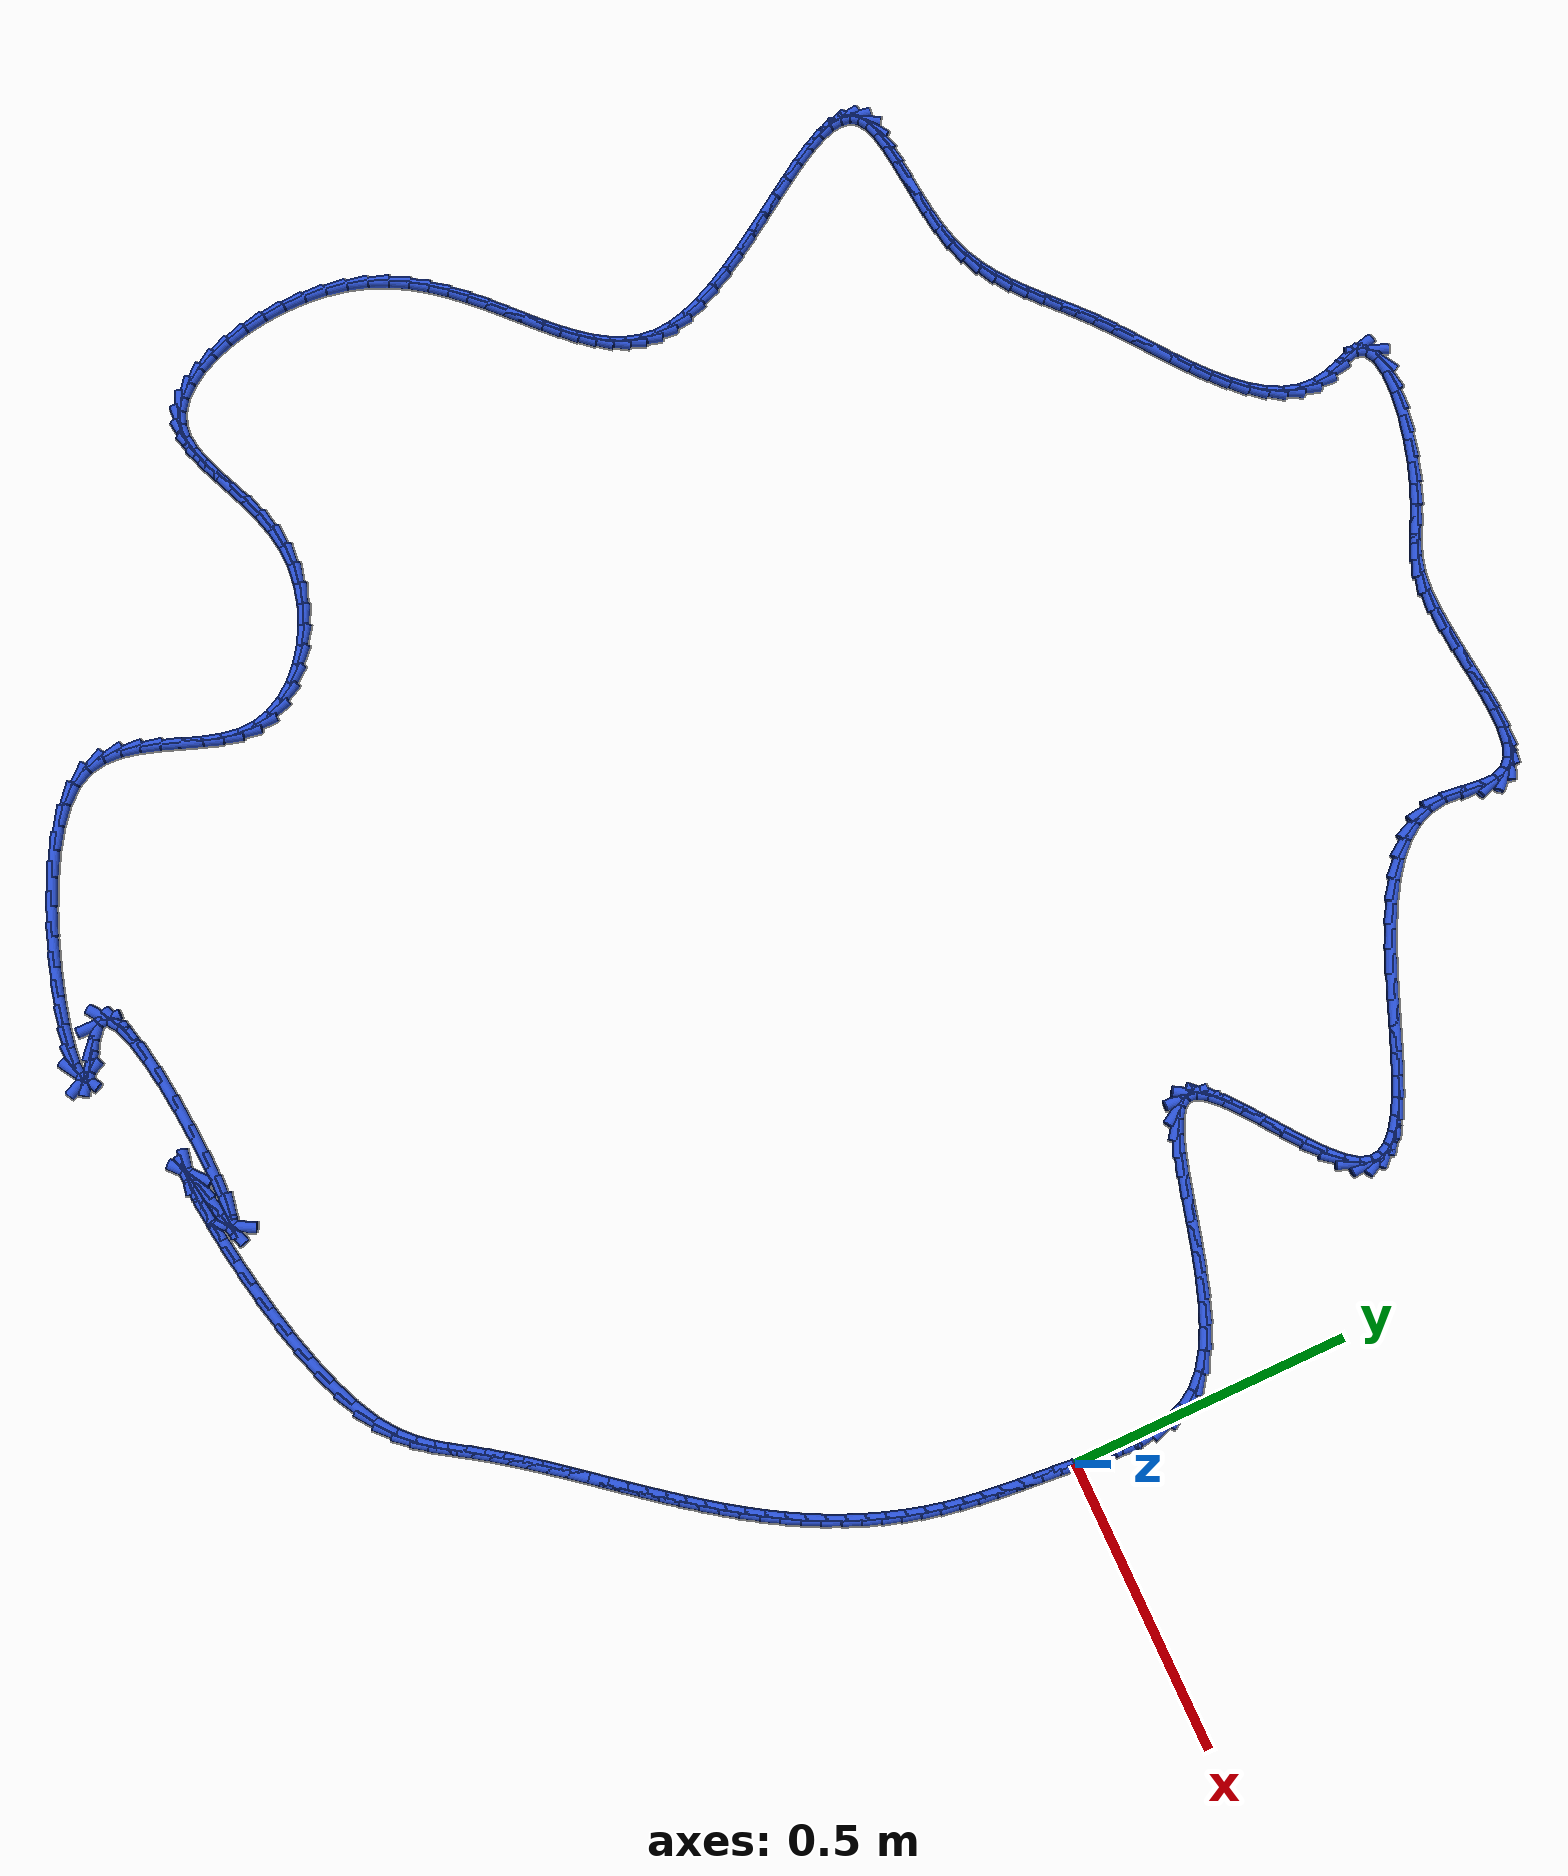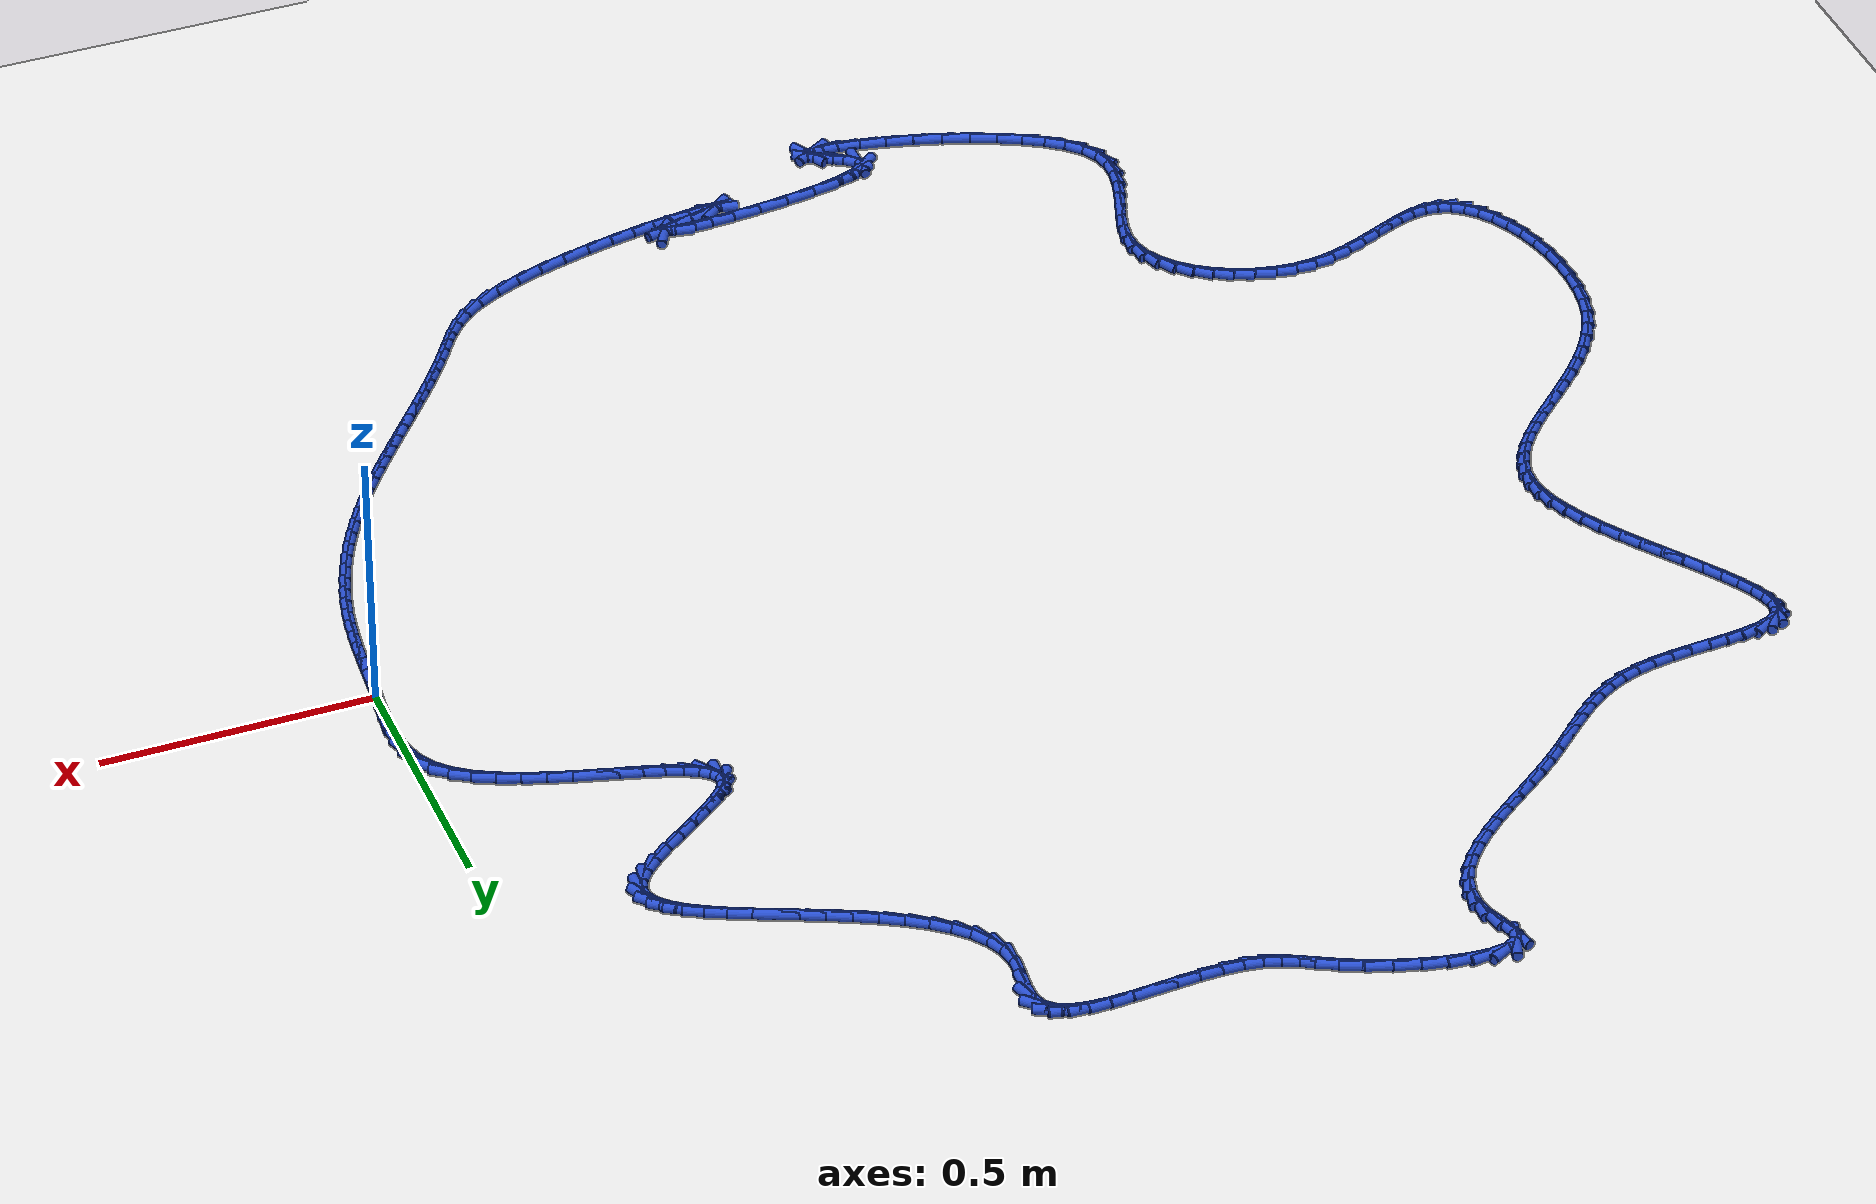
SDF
<sdf version="1.6">
 <world name="default">
  <light name="sun" type="directional">
   <pose>0 0 10 0 -0 0</pose>
   <diffuse>0.8 0.8 0.8 1</diffuse>
   <specular>0.2 0.2 0.2 1</specular>
   <attenuation>
    <range>1000</range>
    <constant>0.9</constant>
    <linear>0.01</linear>
    <quadratic>0.001</quadratic>
   </attenuation>
   <direction>-0.5 0.1 -0.9</direction>
  </light>
  <model name="ground_plane">
   <static>1</static>
   <link name="link">
    <collision name="collision">
     <geometry><plane><normal>0 0 1</normal><size>100 100</size></plane></geometry>
     <surface><friction><ode><mu>100</mu><mu2>50</mu2></ode></friction></surface>
    </collision>
    <visual name="visual">
     <cast_shadows>0</cast_shadows>
     <geometry><plane><normal>0 0 1</normal><size>100 100</size></plane></geometry>
     <material>
      <script><uri>file://media/materials/scripts/gazebo.material</uri><name>Gazebo/WhiteGlow</name></script>
     </material>
    </visual>
   </link>
  </model>
  <gravity>0 0 -9.8</gravity>
  <magnetic_field>6e-06 2.3e-05 -4.2e-05</magnetic_field>
  <atmosphere type="adiabatic"/>
  <physics name="default_physics" default="0" type="ode">
   <max_step_size>0.001</max_step_size>
   <real_time_factor>1</real_time_factor>
   <real_time_update_rate>1000</real_time_update_rate>
  </physics>
  <scene><ambient>0.4 0.4 0.4 1</ambient><background>0.7 0.7 0.7 1</background><shadows>1</shadows></scene>
  <spherical_coordinates>
   <surface_model>EARTH_WGS84</surface_model>
   <latitude_deg>0</latitude_deg>
   <longitude_deg>0</longitude_deg>
   <elevation>0</elevation>
   <heading_deg>0</heading_deg>
  </spherical_coordinates>
  <model name="line">
   <link name="link_0">
    <pose>-5.2909066017292616e-17 -6.938893903907228e-17 0.01 0 1.57 1.4719108549677495</pose>
    <collision name="collision">
     <geometry><cylinder><radius>0.01</radius><length>0.08</length></cylinder></geometry>
    </collision>
    <visual name="visual">
     <material>
      <script><name>Gazebo/Blue</name><uri>file://media/materials/scripts/gazebo.material</uri></script>
     </material>
     <geometry><cylinder><radius>0.01</radius><length>0.08</length></cylinder></geometry>
    </visual>
   </link>
   <link name="link_1">
    <pose>0.0034936658325562106 0.03521519313748598 0.01 0 1.57 1.4887428754856245</pose>
    <collision name="collision">
     <geometry><cylinder><radius>0.01</radius><length>0.08</length></cylinder></geometry>
    </collision>
    <visual name="visual">
     <material>
      <script><name>Gazebo/Blue</name><uri>file://media/materials/scripts/gazebo.material</uri></script>
     </material>
     <geometry><cylinder><radius>0.01</radius><length>0.08</length></cylinder></geometry>
    </visual>
   </link>
   <link name="link_2">
    <pose>0.006408961889988054 0.0706646520076782 0.01 0 1.57 1.536097298039894</pose>
    <collision name="collision">
     <geometry><cylinder><radius>0.01</radius><length>0.08</length></cylinder></geometry>
    </collision>
    <visual name="visual">
     <material>
      <script><name>Gazebo/Blue</name><uri>file://media/materials/scripts/gazebo.material</uri></script>
     </material>
     <geometry><cylinder><radius>0.01</radius><length>0.08</length></cylinder></geometry>
    </visual>
   </link>
   <link name="link_3">
    <pose>0.007626882758057852 0.10575013050941472 0.01 0 1.57 -1.5239868349404162</pose>
    <collision name="collision">
     <geometry><cylinder><radius>0.01</radius><length>0.08</length></cylinder></geometry>
    </collision>
    <visual name="visual">
     <material>
      <script><name>Gazebo/Blue</name><uri>file://media/materials/scripts/gazebo.material</uri></script>
     </material>
     <geometry><cylinder><radius>0.01</radius><length>0.08</length></cylinder></geometry>
    </visual>
   </link>
   <link name="link_4">
    <pose>0.006028423022527976 0.1398733825415338 0.01 0 1.57 -1.4024606938984574</pose>
    <collision name="collision">
     <geometry><cylinder><radius>0.01</radius><length>0.08</length></cylinder></geometry>
    </collision>
    <visual name="visual">
     <material>
      <script><name>Gazebo/Blue</name><uri>file://media/materials/scripts/gazebo.material</uri></script>
     </material>
     <geometry><cylinder><radius>0.01</radius><length>0.08</length></cylinder></geometry>
    </visual>
   </link>
   <link name="link_5">
    <pose>0.0004945772691608008 0.17243616200287354 0.01 0 1.57 -1.2356807022298957</pose>
    <collision name="collision">
     <geometry><cylinder><radius>0.01</radius><length>0.08</length></cylinder></geometry>
    </collision>
    <visual name="visual">
     <material>
      <script><name>Gazebo/Blue</name><uri>file://media/materials/scripts/gazebo.material</uri></script>
     </material>
     <geometry><cylinder><radius>0.01</radius><length>0.08</length></cylinder></geometry>
    </visual>
   </link>
   <link name="link_6">
    <pose>-0.010093659916281299 0.2028402227922723 0.01 0 1.57 -1.0257785120612315</pose>
    <collision name="collision">
     <geometry><cylinder><radius>0.01</radius><length>0.08</length></cylinder></geometry>
    </collision>
    <visual name="visual">
     <material>
      <script><name>Gazebo/Blue</name><uri>file://media/materials/scripts/gazebo.material</uri></script>
     </material>
     <geometry><cylinder><radius>0.01</radius><length>0.08</length></cylinder></geometry>
    </visual>
   </link>
   <link name="link_7">
    <pose>-0.026855293948035965 0.2304873188085681 0.01 0 1.57 -0.8015866358535872</pose>
    <collision name="collision">
     <geometry><cylinder><radius>0.01</radius><length>0.08</length></cylinder></geometry>
    </collision>
    <visual name="visual">
     <material>
      <script><name>Gazebo/Blue</name><uri>file://media/materials/scripts/gazebo.material</uri></script>
     </material>
     <geometry><cylinder><radius>0.01</radius><length>0.08</length></cylinder></geometry>
    </visual>
   </link>
   <link name="link_8">
    <pose>-0.050527521842968964 0.2549386618676007 0.01 0 1.57 -0.624680463261912</pose>
    <collision name="collision">
     <geometry><cylinder><radius>0.01</radius><length>0.08</length></cylinder></geometry>
    </collision>
    <visual name="visual">
     <material>
      <script><name>Gazebo/Blue</name><uri>file://media/materials/scripts/gazebo.material</uri></script>
     </material>
     <geometry><cylinder><radius>0.01</radius><length>0.08</length></cylinder></geometry>
    </visual>
   </link>
   <link name="link_9">
    <pose>-0.08029753828067984 0.27640280456071237 0.01 0 1.57 -0.49808622027171306</pose>
    <collision name="collision">
     <geometry><cylinder><radius>0.01</radius><length>0.08</length></cylinder></geometry>
    </collision>
    <visual name="visual">
     <material>
      <script><name>Gazebo/Blue</name><uri>file://media/materials/scripts/gazebo.material</uri></script>
     </material>
     <geometry><cylinder><radius>0.01</radius><length>0.08</length></cylinder></geometry>
    </visual>
   </link>
   <link name="link_10">
    <pose>-0.11495926056426602 0.2952525472844073 0.01 0 1.57 -0.4087093442081795</pose>
    <collision name="collision">
     <geometry><cylinder><radius>0.01</radius><length>0.08</length></cylinder></geometry>
    </collision>
    <visual name="visual">
     <material>
      <script><name>Gazebo/Blue</name><uri>file://media/materials/scripts/gazebo.material</uri></script>
     </material>
     <geometry><cylinder><radius>0.01</radius><length>0.08</length></cylinder></geometry>
    </visual>
   </link>
   <link name="link_11">
    <pose>-0.15330660595031415 0.31186069045461484 0.01 0 1.57 -0.3464587325183403</pose>
    <collision name="collision">
     <geometry><cylinder><radius>0.01</radius><length>0.08</length></cylinder></geometry>
    </collision>
    <visual name="visual">
     <material>
      <script><name>Gazebo/Blue</name><uri>file://media/materials/scripts/gazebo.material</uri></script>
     </material>
     <geometry><cylinder><radius>0.01</radius><length>0.08</length></cylinder></geometry>
    </visual>
   </link>
   <link name="link_12">
    <pose>-0.19413349169541058 0.32660003448726405 0.01 0 1.57 -0.3047661399730271</pose>
    <collision name="collision">
     <geometry><cylinder><radius>0.01</radius><length>0.08</length></cylinder></geometry>
    </collision>
    <visual name="visual">
     <material>
      <script><name>Gazebo/Blue</name><uri>file://media/materials/scripts/gazebo.material</uri></script>
     </material>
     <geometry><cylinder><radius>0.01</radius><length>0.08</length></cylinder></geometry>
    </visual>
   </link>
   <link name="link_13">
    <pose>-0.23623383505614207 0.3398433797982843 0.01 0 1.57 -0.2798825315152923</pose>
    <collision name="collision">
     <geometry><cylinder><radius>0.01</radius><length>0.08</length></cylinder></geometry>
    </collision>
    <visual name="visual">
     <material>
      <script><name>Gazebo/Blue</name><uri>file://media/materials/scripts/gazebo.material</uri></script>
     </material>
     <geometry><cylinder><radius>0.01</radius><length>0.08</length></cylinder></geometry>
    </visual>
   </link>
   <link name="link_14">
    <pose>-0.2784015532890951 0.35196352680360454 0.01 0 1.57 -0.27033132914279184</pose>
    <collision name="collision">
     <geometry><cylinder><radius>0.01</radius><length>0.08</length></cylinder></geometry>
    </collision>
    <visual name="visual">
     <material>
      <script><name>Gazebo/Blue</name><uri>file://media/materials/scripts/gazebo.material</uri></script>
     </material>
     <geometry><cylinder><radius>0.01</radius><length>0.08</length></cylinder></geometry>
    </visual>
   </link>
   <link name="link_15">
    <pose>-0.3194305636508561 0.363333275919154 0.01 0 1.57 -0.27685356769774777</pose>
    <collision name="collision">
     <geometry><cylinder><radius>0.01</radius><length>0.08</length></cylinder></geometry>
    </collision>
    <visual name="visual">
     <material>
      <script><name>Gazebo/Blue</name><uri>file://media/materials/scripts/gazebo.material</uri></script>
     </material>
     <geometry><cylinder><radius>0.01</radius><length>0.08</length></cylinder></geometry>
    </visual>
   </link>
   <link name="link_16">
    <pose>-0.3581147833980116 0.37432542756086185 0.01 0 1.57 -0.3030970668714215</pose>
    <collision name="collision">
     <geometry><cylinder><radius>0.01</radius><length>0.08</length></cylinder></geometry>
    </collision>
    <visual name="visual">
     <material>
      <script><name>Gazebo/Blue</name><uri>file://media/materials/scripts/gazebo.material</uri></script>
     </material>
     <geometry><cylinder><radius>0.01</radius><length>0.08</length></cylinder></geometry>
    </visual>
   </link>
   <link name="link_17">
    <pose>-0.39324812978714846 0.3853127821446573 0.01 0 1.57 -0.35773735814414226</pose>
    <collision name="collision">
     <geometry><cylinder><radius>0.01</radius><length>0.08</length></cylinder></geometry>
    </collision>
    <visual name="visual">
     <material>
      <script><name>Gazebo/Blue</name><uri>file://media/materials/scripts/gazebo.material</uri></script>
     </material>
     <geometry><cylinder><radius>0.01</radius><length>0.08</length></cylinder></geometry>
    </visual>
   </link>
   <link name="link_18">
    <pose>-0.4236245200748529 0.39666814008646956 0.01 0 1.57 -0.46001962723984324</pose>
    <collision name="collision">
     <geometry><cylinder><radius>0.01</radius><length>0.08</length></cylinder></geometry>
    </collision>
    <visual name="visual">
     <material>
      <script><name>Gazebo/Blue</name><uri>file://media/materials/scripts/gazebo.material</uri></script>
     </material>
     <geometry><cylinder><radius>0.01</radius><length>0.08</length></cylinder></geometry>
    </visual>
   </link>
   <link name="link_19">
    <pose>-0.44803787151771163 0.40876430180222756 0.01 0 1.57 -0.6536877796746867</pose>
    <collision name="collision">
     <geometry><cylinder><radius>0.01</radius><length>0.08</length></cylinder></geometry>
    </collision>
    <visual name="visual">
     <material>
      <script><name>Gazebo/Blue</name><uri>file://media/materials/scripts/gazebo.material</uri></script>
     </material>
     <geometry><cylinder><radius>0.01</radius><length>0.08</length></cylinder></geometry>
    </visual>
   </link>
   <link name="link_20">
    <pose>-0.46528210137231124 0.4219740677078609 0.01 0 1.57 -1.0278129257595885</pose>
    <collision name="collision">
     <geometry><cylinder><radius>0.01</radius><length>0.08</length></cylinder></geometry>
    </collision>
    <visual name="visual">
     <material>
      <script><name>Gazebo/Blue</name><uri>file://media/materials/scripts/gazebo.material</uri></script>
     </material>
     <geometry><cylinder><radius>0.01</radius><length>0.08</length></cylinder></geometry>
    </visual>
   </link>
   <link name="link_21">
    <pose>-0.4741511268952381 0.4366702382192983 0.01 0 1.57 1.5277998645085293</pose>
    <collision name="collision">
     <geometry><cylinder><radius>0.01</radius><length>0.08</length></cylinder></geometry>
    </collision>
    <visual name="visual">
     <material>
      <script><name>Gazebo/Blue</name><uri>file://media/materials/scripts/gazebo.material</uri></script>
     </material>
     <geometry><cylinder><radius>0.01</radius><length>0.08</length></cylinder></geometry>
    </visual>
   </link>
   <link name="link_22">
    <pose>-0.47343886534307883 0.4532256137524693 0.01 0 1.57 1.0379418911633744</pose>
    <collision name="collision">
     <geometry><cylinder><radius>0.01</radius><length>0.08</length></cylinder></geometry>
    </collision>
    <visual name="visual">
     <material>
      <script><name>Gazebo/Blue</name><uri>file://media/materials/scripts/gazebo.material</uri></script>
     </material>
     <geometry><cylinder><radius>0.01</radius><length>0.08</length></cylinder></geometry>
    </visual>
   </link>
   <link name="link_23">
    <pose>-0.4624224345290659 0.47190519831100625 0.01 0 1.57 0.8059604132337853</pose>
    <collision name="collision">
     <geometry><cylinder><radius>0.01</radius><length>0.08</length></cylinder></geometry>
    </collision>
    <visual name="visual">
     <material>
      <script><name>Gazebo/Blue</name><uri>file://media/materials/scripts/gazebo.material</uri></script>
     </material>
     <geometry><cylinder><radius>0.01</radius><length>0.08</length></cylinder></geometry>
    </visual>
   </link>
   <link name="link_24">
    <pose>-0.44269958203866644 0.4924562904442041 0.01 0 1.57 0.7000193351785056</pose>
    <collision name="collision">
     <geometry><cylinder><radius>0.01</radius><length>0.08</length></cylinder></geometry>
    </collision>
    <visual name="visual">
     <material>
      <script><name>Gazebo/Blue</name><uri>file://media/materials/scripts/gazebo.material</uri></script>
     </material>
     <geometry><cylinder><radius>0.01</radius><length>0.08</length></cylinder></geometry>
    </visual>
   </link>
   <link name="link_25">
    <pose>-0.41656387046462906 0.5144709604832284 0.01 0 1.57 0.6514729873845732</pose>
    <collision name="collision">
     <geometry><cylinder><radius>0.01</radius><length>0.08</length></cylinder></geometry>
    </collision>
    <visual name="visual">
     <material>
      <script><name>Gazebo/Blue</name><uri>file://media/materials/scripts/gazebo.material</uri></script>
     </material>
     <geometry><cylinder><radius>0.01</radius><length>0.08</length></cylinder></geometry>
    </visual>
   </link>
   <link name="link_26">
    <pose>-0.3863089936662994 0.5375412494751967 0.01 0 1.57 0.6366369635517307</pose>
    <collision name="collision">
     <geometry><cylinder><radius>0.01</radius><length>0.08</length></cylinder></geometry>
    </collision>
    <visual name="visual">
     <material>
      <script><name>Gazebo/Blue</name><uri>file://media/materials/scripts/gazebo.material</uri></script>
     </material>
     <geometry><cylinder><radius>0.01</radius><length>0.08</length></cylinder></geometry>
    </visual>
   </link>
   <link name="link_27">
    <pose>-0.3542286455030236 0.5612591984672275 0.01 0 1.57 0.6485142569291663</pose>
    <collision name="collision">
     <geometry><cylinder><radius>0.01</radius><length>0.08</length></cylinder></geometry>
    </collision>
    <visual name="visual">
     <material>
      <script><name>Gazebo/Blue</name><uri>file://media/materials/scripts/gazebo.material</uri></script>
     </material>
     <geometry><cylinder><radius>0.01</radius><length>0.08</length></cylinder></geometry>
    </visual>
   </link>
   <link name="link_28">
    <pose>-0.32261651983414713 0.5852168485064382 0.01 0 1.57 0.6895518716663629</pose>
    <collision name="collision">
     <geometry><cylinder><radius>0.01</radius><length>0.08</length></cylinder></geometry>
    </collision>
    <visual name="visual">
     <material>
      <script><name>Gazebo/Blue</name><uri>file://media/materials/scripts/gazebo.material</uri></script>
     </material>
     <geometry><cylinder><radius>0.01</radius><length>0.08</length></cylinder></geometry>
    </visual>
   </link>
   <link name="link_29">
    <pose>-0.293766310519016 0.6090062406399467 0.01 0 1.57 0.7730301202809505</pose>
    <collision name="collision">
     <geometry><cylinder><radius>0.01</radius><length>0.08</length></cylinder></geometry>
    </collision>
    <visual name="visual">
     <material>
      <script><name>Gazebo/Blue</name><uri>file://media/materials/scripts/gazebo.material</uri></script>
     </material>
     <geometry><cylinder><radius>0.01</radius><length>0.08</length></cylinder></geometry>
    </visual>
   </link>
   <link name="link_30">
    <pose>-0.2699717114169761 0.632219415914871 0.01 0 1.57 0.9338470659141276</pose>
    <collision name="collision">
     <geometry><cylinder><radius>0.01</radius><length>0.08</length></cylinder></geometry>
    </collision>
    <visual name="visual">
     <material>
      <script><name>Gazebo/Blue</name><uri>file://media/materials/scripts/gazebo.material</uri></script>
     </material>
     <geometry><cylinder><radius>0.01</radius><length>0.08</length></cylinder></geometry>
    </visual>
   </link>
   <link name="link_31">
    <pose>-0.25352641638737317 0.6544484153783291 0.01 0 1.57 1.23829610941099</pose>
    <collision name="collision">
     <geometry><cylinder><radius>0.01</radius><length>0.08</length></cylinder></geometry>
    </collision>
    <visual name="visual">
     <material>
      <script><name>Gazebo/Blue</name><uri>file://media/materials/scripts/gazebo.material</uri></script>
     </material>
     <geometry><cylinder><radius>0.01</radius><length>0.08</length></cylinder></geometry>
    </visual>
   </link>
   <link name="link_32">
    <pose>-0.24630312031296608 0.6753660539325606 0.01 0 1.57 -1.4824031763894032</pose>
    <collision name="collision">
     <geometry><cylinder><radius>0.01</radius><length>0.08</length></cylinder></geometry>
    </collision>
    <visual name="visual">
     <material>
      <script><name>Gazebo/Blue</name><uri>file://media/materials/scripts/gazebo.material</uri></script>
     </material>
     <geometry><cylinder><radius>0.01</radius><length>0.08</length></cylinder></geometry>
    </visual>
   </link>
   <link name="link_33">
    <pose>-0.24804787297993106 0.695053169616392 0.01 0 1.57 -1.0878005230337855</pose>
    <collision name="collision">
     <geometry><cylinder><radius>0.01</radius><length>0.08</length></cylinder></geometry>
    </collision>
    <visual name="visual">
     <material>
      <script><name>Gazebo/Blue</name><uri>file://media/materials/scripts/gazebo.material</uri></script>
     </material>
     <geometry><cylinder><radius>0.01</radius><length>0.08</length></cylinder></geometry>
    </visual>
   </link>
   <link name="link_34">
    <pose>-0.25783676665433547 0.7137191400962415 0.01 0 1.57 -0.8125861901919864</pose>
    <collision name="collision">
     <geometry><cylinder><radius>0.01</radius><length>0.08</length></cylinder></geometry>
    </collision>
    <visual name="visual">
     <material>
      <script><name>Gazebo/Blue</name><uri>file://media/materials/scripts/gazebo.material</uri></script>
     </material>
     <geometry><cylinder><radius>0.01</radius><length>0.08</length></cylinder></geometry>
    </visual>
   </link>
   <link name="link_35">
    <pose>-0.2747456437343098 0.7315733909787782 0.01 0 1.57 -0.6413767370380604</pose>
    <collision name="collision">
     <geometry><cylinder><radius>0.01</radius><length>0.08</length></cylinder></geometry>
    </collision>
    <visual name="visual">
     <material>
      <script><name>Gazebo/Blue</name><uri>file://media/materials/scripts/gazebo.material</uri></script>
     </material>
     <geometry><cylinder><radius>0.01</radius><length>0.08</length></cylinder></geometry>
    </visual>
   </link>
   <link name="link_36">
    <pose>-0.29785034661798454 0.7488253478706716 0.01 0 1.57 -0.5360878505223857</pose>
    <collision name="collision">
     <geometry><cylinder><radius>0.01</radius><length>0.08</length></cylinder></geometry>
    </collision>
    <visual name="visual">
     <material>
      <script><name>Gazebo/Blue</name><uri>file://media/materials/scripts/gazebo.material</uri></script>
     </material>
     <geometry><cylinder><radius>0.01</radius><length>0.08</length></cylinder></geometry>
    </visual>
   </link>
   <link name="link_37">
    <pose>-0.32622671770348993 0.7656844363785906 0.01 0 1.57 -0.4712873012194078</pose>
    <collision name="collision">
     <geometry><cylinder><radius>0.01</radius><length>0.08</length></cylinder></geometry>
    </collision>
    <visual name="visual">
     <material>
      <script><name>Gazebo/Blue</name><uri>file://media/materials/scripts/gazebo.material</uri></script>
     </material>
     <geometry><cylinder><radius>0.01</radius><length>0.08</length></cylinder></geometry>
    </visual>
   </link>
   <link name="link_38">
    <pose>-0.35895059938895635 0.7823600821092045 0.01 0 1.57 -0.43282481333549855</pose>
    <collision name="collision">
     <geometry><cylinder><radius>0.01</radius><length>0.08</length></cylinder></geometry>
    </collision>
    <visual name="visual">
     <material>
      <script><name>Gazebo/Blue</name><uri>file://media/materials/scripts/gazebo.material</uri></script>
     </material>
     <geometry><cylinder><radius>0.01</radius><length>0.08</length></cylinder></geometry>
    </visual>
   </link>
   <link name="link_39">
    <pose>-0.395097834072514 0.7990617106691822 0.01 0 1.57 -0.41304496454070505</pose>
    <collision name="collision">
     <geometry><cylinder><radius>0.01</radius><length>0.08</length></cylinder></geometry>
    </collision>
    <visual name="visual">
     <material>
      <script><name>Gazebo/Blue</name><uri>file://media/materials/scripts/gazebo.material</uri></script>
     </material>
     <geometry><cylinder><radius>0.01</radius><length>0.08</length></cylinder></geometry>
    </visual>
   </link>
   <link name="link_40">
    <pose>-0.43374426415229317 0.8159987476651931 0.01 0 1.57 -0.4079145702388015</pose>
    <collision name="collision">
     <geometry><cylinder><radius>0.01</radius><length>0.08</length></cylinder></geometry>
    </collision>
    <visual name="visual">
     <material>
      <script><name>Gazebo/Blue</name><uri>file://media/materials/scripts/gazebo.material</uri></script>
     </material>
     <geometry><cylinder><radius>0.01</radius><length>0.08</length></cylinder></geometry>
    </visual>
   </link>
   <link name="link_41">
    <pose>-0.47396573202642484 0.8333806187039067 0.01 0 1.57 -0.4155783640052848</pose>
    <collision name="collision">
     <geometry><cylinder><radius>0.01</radius><length>0.08</length></cylinder></geometry>
    </collision>
    <visual name="visual">
     <material>
      <script><name>Gazebo/Blue</name><uri>file://media/materials/scripts/gazebo.material</uri></script>
     </material>
     <geometry><cylinder><radius>0.01</radius><length>0.08</length></cylinder></geometry>
    </visual>
   </link>
   <link name="link_42">
    <pose>-0.5148380800930389 0.8514167493919916 0.01 0 1.57 -0.4356879050753388</pose>
    <collision name="collision">
     <geometry><cylinder><radius>0.01</radius><length>0.08</length></cylinder></geometry>
    </collision>
    <visual name="visual">
     <material>
      <script><name>Gazebo/Blue</name><uri>file://media/materials/scripts/gazebo.material</uri></script>
     </material>
     <geometry><cylinder><radius>0.01</radius><length>0.08</length></cylinder></geometry>
    </visual>
   </link>
   <link name="link_43">
    <pose>-0.5554371507502659 0.8703165653361173 0.01 0 1.57 -0.46915715959658744</pose>
    <collision name="collision">
     <geometry><cylinder><radius>0.01</radius><length>0.08</length></cylinder></geometry>
    </collision>
    <visual name="visual">
     <material>
      <script><name>Gazebo/Blue</name><uri>file://media/materials/scripts/gazebo.material</uri></script>
     </material>
     <geometry><cylinder><radius>0.01</radius><length>0.08</length></cylinder></geometry>
    </visual>
   </link>
   <link name="link_44">
    <pose>-0.5948387863962358 0.8902894921429527 0.01 0 1.57 -0.5181867321169078</pose>
    <collision name="collision">
     <geometry><cylinder><radius>0.01</radius><length>0.08</length></cylinder></geometry>
    </collision>
    <visual name="visual">
     <material>
      <script><name>Gazebo/Blue</name><uri>file://media/materials/scripts/gazebo.material</uri></script>
     </material>
     <geometry><cylinder><radius>0.01</radius><length>0.08</length></cylinder></geometry>
    </visual>
   </link>
   <link name="link_45">
    <pose>-0.6321188294290794 0.9115449554191674 0.01 0 1.57 -0.5864755261471498</pose>
    <collision name="collision">
     <geometry><cylinder><radius>0.01</radius><length>0.08</length></cylinder></geometry>
    </collision>
    <visual name="visual">
     <material>
      <script><name>Gazebo/Blue</name><uri>file://media/materials/scripts/gazebo.material</uri></script>
     </material>
     <geometry><cylinder><radius>0.01</radius><length>0.08</length></cylinder></geometry>
    </visual>
   </link>
   <link name="link_46">
    <pose>-0.6663531222469266 0.9342923807714302 0.01 0 1.57 -0.6795038261500086</pose>
    <collision name="collision">
     <geometry><cylinder><radius>0.01</radius><length>0.08</length></cylinder></geometry>
    </collision>
    <visual name="visual">
     <material>
      <script><name>Gazebo/Blue</name><uri>file://media/materials/scripts/gazebo.material</uri></script>
     </material>
     <geometry><cylinder><radius>0.01</radius><length>0.08</length></cylinder></geometry>
    </visual>
   </link>
   <link name="link_47">
    <pose>-0.696617507247908 0.9587411938064101 0.01 0 1.57 -0.8045202819315923</pose>
    <collision name="collision">
     <geometry><cylinder><radius>0.01</radius><length>0.08</length></cylinder></geometry>
    </collision>
    <visual name="visual">
     <material>
      <script><name>Gazebo/Blue</name><uri>file://media/materials/scripts/gazebo.material</uri></script>
     </material>
     <geometry><cylinder><radius>0.01</radius><length>0.08</length></cylinder></geometry>
    </visual>
   </link>
   <link name="link_48">
    <pose>-0.7219878268301544 0.9851008201307769 0.01 0 1.57 -0.9691723750278376</pose>
    <collision name="collision">
     <geometry><cylinder><radius>0.01</radius><length>0.08</length></cylinder></geometry>
    </collision>
    <visual name="visual">
     <material>
      <script><name>Gazebo/Blue</name><uri>file://media/materials/scripts/gazebo.material</uri></script>
     </material>
     <geometry><cylinder><radius>0.01</radius><length>0.08</length></cylinder></geometry>
    </visual>
   </link>
   <link name="link_49">
    <pose>-0.7415399233917956 1.0135806853511995 0.01 0 1.57 -1.176768428785357</pose>
    <collision name="collision">
     <geometry><cylinder><radius>0.01</radius><length>0.08</length></cylinder></geometry>
    </collision>
    <visual name="visual">
     <material>
      <script><name>Gazebo/Blue</name><uri>file://media/materials/scripts/gazebo.material</uri></script>
     </material>
     <geometry><cylinder><radius>0.01</radius><length>0.08</length></cylinder></geometry>
    </visual>
   </link>
   <link name="link_50">
    <pose>-0.7543496393309623 1.0443902150743467 0.01 0 1.57 -1.4177364187366572</pose>
    <collision name="collision">
     <geometry><cylinder><radius>0.01</radius><length>0.08</length></cylinder></geometry>
    </collision>
    <visual name="visual">
     <material>
      <script><name>Gazebo/Blue</name><uri>file://media/materials/scripts/gazebo.material</uri></script>
     </material>
     <geometry><cylinder><radius>0.01</radius><length>0.08</length></cylinder></geometry>
    </visual>
   </link>
   <link name="link_51">
    <pose>-0.7594941079737318 1.0777381511347617 0.01 0 1.57 1.5157177939530706</pose>
    <collision name="collision">
     <geometry><cylinder><radius>0.01</radius><length>0.08</length></cylinder></geometry>
    </collision>
    <visual name="visual">
     <material>
      <script><name>Gazebo/Blue</name><uri>file://media/materials/scripts/gazebo.material</uri></script>
     </material>
     <geometry><cylinder><radius>0.01</radius><length>0.08</length></cylinder></geometry>
    </visual>
   </link>
   <link name="link_52">
    <pose>-0.7575477567469486 1.1130401562696568 0.01 0 1.57 1.4526006844129304</pose>
    <collision name="collision">
     <geometry><cylinder><radius>0.01</radius><length>0.08</length></cylinder></geometry>
    </collision>
    <visual name="visual">
     <material>
      <script><name>Gazebo/Blue</name><uri>file://media/materials/scripts/gazebo.material</uri></script>
     </material>
     <geometry><cylinder><radius>0.01</radius><length>0.08</length></cylinder></geometry>
    </visual>
   </link>
   <link name="link_53">
    <pose>-0.7534687496534659 1.1473899380005947 0.01 0 1.57 1.555651029430251</pose>
    <collision name="collision">
     <geometry><cylinder><radius>0.01</radius><length>0.08</length></cylinder></geometry>
    </collision>
    <visual name="visual">
     <material>
      <script><name>Gazebo/Blue</name><uri>file://media/materials/scripts/gazebo.material</uri></script>
     </material>
     <geometry><cylinder><radius>0.01</radius><length>0.08</length></cylinder></geometry>
    </visual>
   </link>
   <link name="link_54">
    <pose>-0.7530133177027126 1.17745848779031 0.01 0 1.57 -1.234655585837399</pose>
    <collision name="collision">
     <geometry><cylinder><radius>0.01</radius><length>0.08</length></cylinder></geometry>
    </collision>
    <visual name="visual">
     <material>
      <script><name>Gazebo/Blue</name><uri>file://media/materials/scripts/gazebo.material</uri></script>
     </material>
     <geometry><cylinder><radius>0.01</radius><length>0.08</length></cylinder></geometry>
    </visual>
   </link>
   <link name="link_55">
    <pose>-0.761053278528035 1.2004692113534723 0.01 0 1.57 -0.7640641620262352</pose>
    <collision name="collision">
     <geometry><cylinder><radius>0.01</radius><length>0.08</length></cylinder></geometry>
    </collision>
    <visual name="visual">
     <material>
      <script><name>Gazebo/Blue</name><uri>file://media/materials/scripts/gazebo.material</uri></script>
     </material>
     <geometry><cylinder><radius>0.01</radius><length>0.08</length></cylinder></geometry>
    </visual>
   </link>
   <link name="link_56">
    <pose>-0.7778254460534036 1.2165405883329337 0.01 0 1.57 -0.39832741358225426</pose>
    <collision name="collision">
     <geometry><cylinder><radius>0.01</radius><length>0.08</length></cylinder></geometry>
    </collision>
    <visual name="visual">
     <material>
      <script><name>Gazebo/Blue</name><uri>file://media/materials/scripts/gazebo.material</uri></script>
     </material>
     <geometry><cylinder><radius>0.01</radius><length>0.08</length></cylinder></geometry>
    </visual>
   </link>
   <link name="link_57">
    <pose>-0.8020534108696513 1.226736274188868 0.01 0 1.57 -0.17525654782136993</pose>
    <collision name="collision">
     <geometry><cylinder><radius>0.01</radius><length>0.08</length></cylinder></geometry>
    </collision>
    <visual name="visual">
     <material>
      <script><name>Gazebo/Blue</name><uri>file://media/materials/scripts/gazebo.material</uri></script>
     </material>
     <geometry><cylinder><radius>0.01</radius><length>0.08</length></cylinder></geometry>
    </visual>
   </link>
   <link name="link_58">
    <pose>-0.8324599191438589 1.2321204518177424 0.01 0 1.57 -0.04632634324566324</pose>
    <collision name="collision">
     <geometry><cylinder><radius>0.01</radius><length>0.08</length></cylinder></geometry>
    </collision>
    <visual name="visual">
     <material>
      <script><name>Gazebo/Blue</name><uri>file://media/materials/scripts/gazebo.material</uri></script>
     </material>
     <geometry><cylinder><radius>0.01</radius><length>0.08</length></cylinder></geometry>
    </visual>
   </link>
   <link name="link_59">
    <pose>-0.8677677170431066 1.233757304116026 0.01 0 1.57 0.02686845820907022</pose>
    <collision name="collision">
     <geometry><cylinder><radius>0.01</radius><length>0.08</length></cylinder></geometry>
    </collision>
    <visual name="visual">
     <material>
      <script><name>Gazebo/Blue</name><uri>file://media/materials/scripts/gazebo.material</uri></script>
     </material>
     <geometry><cylinder><radius>0.01</radius><length>0.08</length></cylinder></geometry>
    </visual>
   </link>
   <link name="link_60">
    <pose>-0.9066995507344761 1.2327110139801867 0.01 0 1.57 0.06447782014905086</pose>
    <collision name="collision">
     <geometry><cylinder><radius>0.01</radius><length>0.08</length></cylinder></geometry>
    </collision>
    <visual name="visual">
     <material>
      <script><name>Gazebo/Blue</name><uri>file://media/materials/scripts/gazebo.material</uri></script>
     </material>
     <geometry><cylinder><radius>0.01</radius><length>0.08</length></cylinder></geometry>
    </visual>
   </link>
   <link name="link_61">
    <pose>-0.9479781663850473 1.2300457643066922 0.01 0 1.57 0.07589097898877292</pose>
    <collision name="collision">
     <geometry><cylinder><radius>0.01</radius><length>0.08</length></cylinder></geometry>
    </collision>
    <visual name="visual">
     <material>
      <script><name>Gazebo/Blue</name><uri>file://media/materials/scripts/gazebo.material</uri></script>
     </material>
     <geometry><cylinder><radius>0.01</radius><length>0.08</length></cylinder></geometry>
    </visual>
   </link>
   <link name="link_62">
    <pose>-0.9903263101619011 1.2268257379920116 0.01 0 1.57 0.06423502722498765</pose>
    <collision name="collision">
     <geometry><cylinder><radius>0.01</radius><length>0.08</length></cylinder></geometry>
    </collision>
    <visual name="visual">
     <material>
      <script><name>Gazebo/Blue</name><uri>file://media/materials/scripts/gazebo.material</uri></script>
     </material>
     <geometry><cylinder><radius>0.01</radius><length>0.08</length></cylinder></geometry>
    </visual>
   </link>
   <link name="link_63">
    <pose>-1.0324667282321192 1.2241151179326133 0.01 0 1.57 0.027960209830228892</pose>
    <collision name="collision">
     <geometry><cylinder><radius>0.01</radius><length>0.08</length></cylinder></geometry>
    </collision>
    <visual name="visual">
     <material>
      <script><name>Gazebo/Blue</name><uri>file://media/materials/scripts/gazebo.material</uri></script>
     </material>
     <geometry><cylinder><radius>0.01</radius><length>0.08</length></cylinder></geometry>
    </visual>
   </link>
   <link name="link_64">
    <pose>-1.0731221667627815 1.2229780870249645 0.01 0 1.57 -0.03958380470929589</pose>
    <collision name="collision">
     <geometry><cylinder><radius>0.01</radius><length>0.08</length></cylinder></geometry>
    </collision>
    <visual name="visual">
     <material>
      <script><name>Gazebo/Blue</name><uri>file://media/materials/scripts/gazebo.material</uri></script>
     </material>
     <geometry><cylinder><radius>0.01</radius><length>0.08</length></cylinder></geometry>
    </visual>
   </link>
   <link name="link_65">
    <pose>-1.1110153719209692 1.2244788281655348 0.01 0 1.57 -0.15201765976364542</pose>
    <collision name="collision">
     <geometry><cylinder><radius>0.01</radius><length>0.08</length></cylinder></geometry>
    </collision>
    <visual name="visual">
     <material>
      <script><name>Gazebo/Blue</name><uri>file://media/materials/scripts/gazebo.material</uri></script>
     </material>
     <geometry><cylinder><radius>0.01</radius><length>0.08</length></cylinder></geometry>
    </visual>
   </link>
   <link name="link_66">
    <pose>-1.144891387799129 1.2296686201536204 0.01 0 1.57 -0.29835471026319677</pose>
    <collision name="collision">
     <geometry><cylinder><radius>0.01</radius><length>0.08</length></cylinder></geometry>
    </collision>
    <visual name="visual">
     <material>
      <script><name>Gazebo/Blue</name><uri>file://media/materials/scripts/gazebo.material</uri></script>
     </material>
     <geometry><cylinder><radius>0.01</radius><length>0.08</length></cylinder></geometry>
    </visual>
   </link>
   <link name="link_67">
    <pose>-1.1747741862152925 1.2388586098087726 0.01 0 1.57 -0.4179214696370899</pose>
    <collision name="collision">
     <geometry><cylinder><radius>0.01</radius><length>0.08</length></cylinder></geometry>
    </collision>
    <visual name="visual">
     <material>
      <script><name>Gazebo/Blue</name><uri>file://media/materials/scripts/gazebo.material</uri></script>
     </material>
     <geometry><cylinder><radius>0.01</radius><length>0.08</length></cylinder></geometry>
    </visual>
   </link>
   <link name="link_68">
    <pose>-1.2026369050497732 1.2512319363957192 0.01 0 1.57 -0.482204271727391</pose>
    <collision name="collision">
     <geometry><cylinder><radius>0.01</radius><length>0.08</length></cylinder></geometry>
    </collision>
    <visual name="visual">
     <material>
      <script><name>Gazebo/Blue</name><uri>file://media/materials/scripts/gazebo.material</uri></script>
     </material>
     <geometry><cylinder><radius>0.01</radius><length>0.08</length></cylinder></geometry>
    </visual>
   </link>
   <link name="link_69">
    <pose>-1.2306165343958104 1.2658769157890049 0.01 0 1.57 -0.48687240520562197</pose>
    <collision name="collision">
     <geometry><cylinder><radius>0.01</radius><length>0.08</length></cylinder></geometry>
    </collision>
    <visual name="visual">
     <material>
      <script><name>Gazebo/Blue</name><uri>file://media/materials/scripts/gazebo.material</uri></script>
     </material>
     <geometry><cylinder><radius>0.01</radius><length>0.08</length></cylinder></geometry>
    </visual>
   </link>
   <link name="link_70">
    <pose>-1.2608500643466436 1.2818818638631737 0.01 0 1.57 -0.4436046245265949</pose>
    <collision name="collision">
     <geometry><cylinder><radius>0.01</radius><length>0.08</length></cylinder></geometry>
    </collision>
    <visual name="visual">
     <material>
      <script><name>Gazebo/Blue</name><uri>file://media/materials/scripts/gazebo.material</uri></script>
     </material>
     <geometry><cylinder><radius>0.01</radius><length>0.08</length></cylinder></geometry>
    </visual>
   </link>
   <link name="link_71">
    <pose>-1.2954744849955138 1.2983350964927705 0.01 0 1.57 -0.37551782669026795</pose>
    <collision name="collision">
     <geometry><cylinder><radius>0.01</radius><length>0.08</length></cylinder></geometry>
    </collision>
    <visual name="visual">
     <material>
      <script><name>Gazebo/Blue</name><uri>file://media/materials/scripts/gazebo.material</uri></script>
     </material>
     <geometry><cylinder><radius>0.01</radius><length>0.08</length></cylinder></geometry>
    </visual>
   </link>
   <link name="link_72">
    <pose>-1.3359453183276713 1.314289700954569 0.01 0 1.57 -0.312136390125347</pose>
    <collision name="collision">
     <geometry><cylinder><radius>0.01</radius><length>0.08</length></cylinder></geometry>
    </collision>
    <visual name="visual">
     <material>
      <script><name>Gazebo/Blue</name><uri>file://media/materials/scripts/gazebo.material</uri></script>
     </material>
     <geometry><cylinder><radius>0.01</radius><length>0.08</length></cylinder></geometry>
    </visual>
   </link>
   <link name="link_73">
    <pose>-1.3803730166859505 1.328625840640038 0.01 0 1.57 -0.24864488955590802</pose>
    <collision name="collision">
     <geometry><cylinder><radius>0.01</radius><length>0.08</length></cylinder></geometry>
    </collision>
    <visual name="visual">
     <material>
      <script><name>Gazebo/Blue</name><uri>file://media/materials/scripts/gazebo.material</uri></script>
     </material>
     <geometry><cylinder><radius>0.01</radius><length>0.08</length></cylinder></geometry>
    </visual>
   </link>
   <link name="link_74">
    <pose>-1.4258433351603816 1.3401707070598883 0.01 0 1.57 -0.17215598530925108</pose>
    <collision name="collision">
     <geometry><cylinder><radius>0.01</radius><length>0.08</length></cylinder></geometry>
    </collision>
    <visual name="visual">
     <material>
      <script><name>Gazebo/Blue</name><uri>file://media/materials/scripts/gazebo.material</uri></script>
     </material>
     <geometry><cylinder><radius>0.01</radius><length>0.08</length></cylinder></geometry>
    </visual>
   </link>
   <link name="link_75">
    <pose>-1.469441763519032 1.3477514780089723 0.01 0 1.57 -0.06288337123225225</pose>
    <collision name="collision">
     <geometry><cylinder><radius>0.01</radius><length>0.08</length></cylinder></geometry>
    </collision>
    <visual name="visual">
     <material>
      <script><name>Gazebo/Blue</name><uri>file://media/materials/scripts/gazebo.material</uri></script>
     </material>
     <geometry><cylinder><radius>0.01</radius><length>0.08</length></cylinder></geometry>
    </visual>
   </link>
   <link name="link_76">
    <pose>-1.5082537915299699 1.3501953312821426 0.01 0 1.57 0.12362691928695003</pose>
    <collision name="collision">
     <geometry><cylinder><radius>0.01</radius><length>0.08</length></cylinder></geometry>
    </collision>
    <visual name="visual">
     <material>
      <script><name>Gazebo/Blue</name><uri>file://media/materials/scripts/gazebo.material</uri></script>
     </material>
     <geometry><cylinder><radius>0.01</radius><length>0.08</length></cylinder></geometry>
    </visual>
   </link>
   <link name="link_77">
    <pose>-1.5393649089612629 1.346329444674252 0.01 0 1.57 0.5056787712496645</pose>
    <collision name="collision">
     <geometry><cylinder><radius>0.01</radius><length>0.08</length></cylinder></geometry>
    </collision>
    <visual name="visual">
     <material>
      <script><name>Gazebo/Blue</name><uri>file://media/materials/scripts/gazebo.material</uri></script>
     </material>
     <geometry><cylinder><radius>0.01</radius><length>0.08</length></cylinder></geometry>
    </visual>
   </link>
   <link name="link_78">
    <pose>-1.5598606055809792 1.3349809959801524 0.01 0 1.57 1.2357067571721632</pose>
    <collision name="collision">
     <geometry><cylinder><radius>0.01</radius><length>0.08</length></cylinder></geometry>
    </collision>
    <visual name="visual">
     <material>
      <script><name>Gazebo/Blue</name><uri>file://media/materials/scripts/gazebo.material</uri></script>
     </material>
     <geometry><cylinder><radius>0.01</radius><length>0.08</length></cylinder></geometry>
    </visual>
   </link>
   <link name="link_79">
    <pose>-1.5668263711571861 1.3149771629946962 0.01 0 1.57 -1.3102529220117867</pose>
    <collision name="collision">
     <geometry><cylinder><radius>0.01</radius><length>0.08</length></cylinder></geometry>
    </collision>
    <visual name="visual">
     <material>
      <script><name>Gazebo/Blue</name><uri>file://media/materials/scripts/gazebo.material</uri></script>
     </material>
     <geometry><cylinder><radius>0.01</radius><length>0.08</length></cylinder></geometry>
    </visual>
   </link>
   <link name="link_80">
    <pose>-1.5590845135645393 1.2859383169284322 0.01 0 1.57 -1.2259217823920447</pose>
    <collision name="collision">
     <geometry><cylinder><radius>0.01</radius><length>0.08</length></cylinder></geometry>
    </collision>
    <visual name="visual">
     <material>
      <script><name>Gazebo/Blue</name><uri>file://media/materials/scripts/gazebo.material</uri></script>
     </material>
     <geometry><cylinder><radius>0.01</radius><length>0.08</length></cylinder></geometry>
    </visual>
   </link>
   <link name="link_81">
    <pose>-1.5471968218310541 1.2528462525622603 0.01 0 1.57 -1.4088029715980532</pose>
    <collision name="collision">
     <geometry><cylinder><radius>0.01</radius><length>0.08</length></cylinder></geometry>
    </collision>
    <visual name="visual">
     <material>
      <script><name>Gazebo/Blue</name><uri>file://media/materials/scripts/gazebo.material</uri></script>
     </material>
     <geometry><cylinder><radius>0.01</radius><length>0.08</length></cylinder></geometry>
    </visual>
   </link>
   <link name="link_82">
    <pose>-1.5419606893578979 1.220806356800604 0.01 0 1.57 1.505582988976819</pose>
    <collision name="collision">
     <geometry><cylinder><radius>0.01</radius><length>0.08</length></cylinder></geometry>
    </collision>
    <visual name="visual">
     <material>
      <script><name>Gazebo/Blue</name><uri>file://media/materials/scripts/gazebo.material</uri></script>
     </material>
     <geometry><cylinder><radius>0.01</radius><length>0.08</length></cylinder></geometry>
    </visual>
   </link>
   <link name="link_83">
    <pose>-1.543953468428901 1.190291842647732 0.01 0 1.57 1.2890413868446606</pose>
    <collision name="collision">
     <geometry><cylinder><radius>0.01</radius><length>0.08</length></cylinder></geometry>
    </collision>
    <visual name="visual">
     <material>
      <script><name>Gazebo/Blue</name><uri>file://media/materials/scripts/gazebo.material</uri></script>
     </material>
     <geometry><cylinder><radius>0.01</radius><length>0.08</length></cylinder></geometry>
    </visual>
   </link>
   <link name="link_84">
    <pose>-1.5523867369889974 1.1611568866221043 0.01 0 1.57 1.103293261546374</pose>
    <collision name="collision">
     <geometry><cylinder><radius>0.01</radius><length>0.08</length></cylinder></geometry>
    </collision>
    <visual name="visual">
     <material>
      <script><name>Gazebo/Blue</name><uri>file://media/materials/scripts/gazebo.material</uri></script>
     </material>
     <geometry><cylinder><radius>0.01</radius><length>0.08</length></cylinder></geometry>
    </visual>
   </link>
   <link name="link_85">
    <pose>-1.5664720729831216 1.13325566524218 0.01 0 1.57 0.9555874834113489</pose>
    <collision name="collision">
     <geometry><cylinder><radius>0.01</radius><length>0.08</length></cylinder></geometry>
    </collision>
    <visual name="visual">
     <material>
      <script><name>Gazebo/Blue</name><uri>file://media/materials/scripts/gazebo.material</uri></script>
     </material>
     <geometry><cylinder><radius>0.01</radius><length>0.08</length></cylinder></geometry>
    </visual>
   </link>
   <link name="link_86">
    <pose>-1.5854210543562077 1.1064423550264177 0.01 0 1.57 0.8435591626753717</pose>
    <collision name="collision">
     <geometry><cylinder><radius>0.01</radius><length>0.08</length></cylinder></geometry>
    </collision>
    <visual name="visual">
     <material>
      <script><name>Gazebo/Blue</name><uri>file://media/materials/scripts/gazebo.material</uri></script>
     </material>
     <geometry><cylinder><radius>0.01</radius><length>0.08</length></cylinder></geometry>
    </visual>
   </link>
   <link name="link_87">
    <pose>-1.6084452590531906 1.0805711324932776 0.01 0 1.57 0.7613486133042878</pose>
    <collision name="collision">
     <geometry><cylinder><radius>0.01</radius><length>0.08</length></cylinder></geometry>
    </collision>
    <visual name="visual">
     <material>
      <script><name>Gazebo/Blue</name><uri>file://media/materials/scripts/gazebo.material</uri></script>
     </material>
     <geometry><cylinder><radius>0.01</radius><length>0.08</length></cylinder></geometry>
    </visual>
   </link>
   <link name="link_88">
    <pose>-1.6347562650190037 1.0554961741612183 0.01 0 1.57 0.7032138651859747</pose>
    <collision name="collision">
     <geometry><cylinder><radius>0.01</radius><length>0.08</length></cylinder></geometry>
    </collision>
    <visual name="visual">
     <material>
      <script><name>Gazebo/Blue</name><uri>file://media/materials/scripts/gazebo.material</uri></script>
     </material>
     <geometry><cylinder><radius>0.01</radius><length>0.08</length></cylinder></geometry>
    </visual>
   </link>
   <link name="link_89">
    <pose>-1.6635656501985823 1.0310716565487 0.01 0 1.57 0.6647609921291191</pose>
    <collision name="collision">
     <geometry><cylinder><radius>0.01</radius><length>0.08</length></cylinder></geometry>
    </collision>
    <visual name="visual">
     <material>
      <script><name>Gazebo/Blue</name><uri>file://media/materials/scripts/gazebo.material</uri></script>
     </material>
     <geometry><cylinder><radius>0.01</radius><length>0.08</length></cylinder></geometry>
    </visual>
   </link>
   <link name="link_90">
    <pose>-1.6940849925368597 1.007151756174181 0.01 0 1.57 0.643103006927699</pose>
    <collision name="collision">
     <geometry><cylinder><radius>0.01</radius><length>0.08</length></cylinder></geometry>
    </collision>
    <visual name="visual">
     <material>
      <script><name>Gazebo/Blue</name><uri>file://media/materials/scripts/gazebo.material</uri></script>
     </material>
     <geometry><cylinder><radius>0.01</radius><length>0.08</length></cylinder></geometry>
    </visual>
   </link>
   <link name="link_91">
    <pose>-1.7255258699787703 0.9835906495561211 0.01 0 1.57 0.6367301845250591</pose>
    <collision name="collision">
     <geometry><cylinder><radius>0.01</radius><length>0.08</length></cylinder></geometry>
    </collision>
    <visual name="visual">
     <material>
      <script><name>Gazebo/Blue</name><uri>file://media/materials/scripts/gazebo.material</uri></script>
     </material>
     <geometry><cylinder><radius>0.01</radius><length>0.08</length></cylinder></geometry>
    </visual>
   </link>
   <link name="link_92">
    <pose>-1.7570998604692494 0.9602425132129794 0.01 0 1.57 0.6454022956828109</pose>
    <collision name="collision">
     <geometry><cylinder><radius>0.01</radius><length>0.08</length></cylinder></geometry>
    </collision>
    <visual name="visual">
     <material>
      <script><name>Gazebo/Blue</name><uri>file://media/materials/scripts/gazebo.material</uri></script>
     </material>
     <geometry><cylinder><radius>0.01</radius><length>0.08</length></cylinder></geometry>
    </visual>
   </link>
   <link name="link_93">
    <pose>-1.7880185419532306 0.9369615236632152 0.01 0 1.57 0.670166382172441</pose>
    <collision name="collision">
     <geometry><cylinder><radius>0.01</radius><length>0.08</length></cylinder></geometry>
    </collision>
    <visual name="visual">
     <material>
      <script><name>Gazebo/Blue</name><uri>file://media/materials/scripts/gazebo.material</uri></script>
     </material>
     <geometry><cylinder><radius>0.01</radius><length>0.08</length></cylinder></geometry>
    </visual>
   </link>
   <link name="link_94">
    <pose>-1.817493518385247 0.9136018672250995 0.01 0 1.57 0.7065677783787276</pose>
    <collision name="collision">
     <geometry><cylinder><radius>0.01</radius><length>0.08</length></cylinder></geometry>
    </collision>
    <visual name="visual">
     <material>
      <script><name>Gazebo/Blue</name><uri>file://media/materials/scripts/gazebo.material</uri></script>
     </material>
     <geometry><cylinder><radius>0.01</radius><length>0.08</length></cylinder></geometry>
    </visual>
   </link>
   <link name="link_95">
    <pose>-1.8450047798313687 0.8901188518612219 0.01 0 1.57 0.7315258379015893</pose>
    <collision name="collision">
     <geometry><cylinder><radius>0.01</radius><length>0.08</length></cylinder></geometry>
    </collision>
    <visual name="visual">
     <material>
      <script><name>Gazebo/Blue</name><uri>file://media/materials/scripts/gazebo.material</uri></script>
     </material>
     <geometry><cylinder><radius>0.01</radius><length>0.08</length></cylinder></geometry>
    </visual>
   </link>
   <link name="link_96">
    <pose>-1.870961833466025 0.8668180059605606 0.01 0 1.57 0.7377687750351198</pose>
    <collision name="collision">
     <geometry><cylinder><radius>0.01</radius><length>0.08</length></cylinder></geometry>
    </collision>
    <visual name="visual">
     <material>
      <script><name>Gazebo/Blue</name><uri>file://media/materials/scripts/gazebo.material</uri></script>
     </material>
     <geometry><cylinder><radius>0.01</radius><length>0.08</length></cylinder></geometry>
    </visual>
   </link>
   <link name="link_97">
    <pose>-1.8959752786860415 0.8440806247842013 0.01 0 1.57 0.7233384059626737</pose>
    <collision name="collision">
     <geometry><cylinder><radius>0.01</radius><length>0.08</length></cylinder></geometry>
    </collision>
    <visual name="visual">
     <material>
      <script><name>Gazebo/Blue</name><uri>file://media/materials/scripts/gazebo.material</uri></script>
     </material>
     <geometry><cylinder><radius>0.01</radius><length>0.08</length></cylinder></geometry>
    </visual>
   </link>
   <link name="link_98">
    <pose>-1.9206557148882464 0.8222880035932311 0.01 0 1.57 0.6868412274657975</pose>
    <collision name="collision">
     <geometry><cylinder><radius>0.01</radius><length>0.08</length></cylinder></geometry>
    </collision>
    <visual name="visual">
     <material>
      <script><name>Gazebo/Blue</name><uri>file://media/materials/scripts/gazebo.material</uri></script>
     </material>
     <geometry><cylinder><radius>0.01</radius><length>0.08</length></cylinder></geometry>
    </visual>
   </link>
   <link name="link_99">
    <pose>-1.9456137414694663 0.8018214376487361 0.01 0 1.57 0.6278331691102371</pose>
    <collision name="collision">
     <geometry><cylinder><radius>0.01</radius><length>0.08</length></cylinder></geometry>
    </collision>
    <visual name="visual">
     <material>
      <script><name>Gazebo/Blue</name><uri>file://media/materials/scripts/gazebo.material</uri></script>
     </material>
     <geometry><cylinder><radius>0.01</radius><length>0.08</length></cylinder></geometry>
    </visual>
   </link>
   <link name="link_100">
    <pose>-1.9714599578265284 0.7830622222118029 0.01 0 1.57 0.5474765469927761</pose>
    <collision name="collision">
     <geometry><cylinder><radius>0.01</radius><length>0.08</length></cylinder></geometry>
    </collision>
    <visual name="visual">
     <material>
      <script><name>Gazebo/Blue</name><uri>file://media/materials/scripts/gazebo.material</uri></script>
     </material>
     <geometry><cylinder><radius>0.01</radius><length>0.08</length></cylinder></geometry>
    </visual>
   </link>
   <link name="link_101">
    <pose>-1.9988049633562595 0.7663916525435179 0.01 0 1.57 0.44924366442053265</pose>
    <collision name="collision">
     <geometry><cylinder><radius>0.01</radius><length>0.08</length></cylinder></geometry>
    </collision>
    <visual name="visual">
     <material>
      <script><name>Gazebo/Blue</name><uri>file://media/materials/scripts/gazebo.material</uri></script>
     </material>
     <geometry><cylinder><radius>0.01</radius><length>0.08</length></cylinder></geometry>
    </visual>
   </link>
   <link name="link_102">
    <pose>-2.0282593574554864 0.7521910239049677 0.01 0 1.57 0.3391192617183183</pose>
    <collision name="collision">
     <geometry><cylinder><radius>0.01</radius><length>0.08</length></cylinder></geometry>
    </collision>
    <visual name="visual">
     <material>
      <script><name>Gazebo/Blue</name><uri>file://media/materials/scripts/gazebo.material</uri></script>
     </material>
     <geometry><cylinder><radius>0.01</radius><length>0.08</length></cylinder></geometry>
    </visual>
   </link>
   <link name="link_103">
    <pose>-2.0604337395210375 0.7408416315572388 0.01 0 1.57 0.22853827593893122</pose>
    <collision name="collision">
     <geometry><cylinder><radius>0.01</radius><length>0.08</length></cylinder></geometry>
    </collision>
    <visual name="visual">
     <material>
      <script><name>Gazebo/Blue</name><uri>file://media/materials/scripts/gazebo.material</uri></script>
     </material>
     <geometry><cylinder><radius>0.01</radius><length>0.08</length></cylinder></geometry>
    </visual>
   </link>
   <link name="link_104">
    <pose>-2.0957757211422177 0.7326210149425776 0.01 0 1.57 0.14710145297666546</pose>
    <collision name="collision">
     <geometry><cylinder><radius>0.01</radius><length>0.08</length></cylinder></geometry>
    </collision>
    <visual name="visual">
     <material>
      <script><name>Gazebo/Blue</name><uri>file://media/materials/scripts/gazebo.material</uri></script>
     </material>
     <geometry><cylinder><radius>0.01</radius><length>0.08</length></cylinder></geometry>
    </visual>
   </link>
   <link name="link_105">
    <pose>-2.133512086685349 0.7270295515172545 0.01 0 1.57 0.09798317878341813</pose>
    <collision name="collision">
     <geometry><cylinder><radius>0.01</radius><length>0.08</length></cylinder></geometry>
    </collision>
    <visual name="visual">
     <material>
      <script><name>Gazebo/Blue</name><uri>file://media/materials/scripts/gazebo.material</uri></script>
     </material>
     <geometry><cylinder><radius>0.01</radius><length>0.08</length></cylinder></geometry>
    </visual>
   </link>
   <link name="link_106">
    <pose>-2.172316019957649 0.7232152041600719 0.01 0 1.57 0.07486953056015273</pose>
    <collision name="collision">
     <geometry><cylinder><radius>0.01</radius><length>0.08</length></cylinder></geometry>
    </collision>
    <visual name="visual">
     <material>
      <script><name>Gazebo/Blue</name><uri>file://media/materials/scripts/gazebo.material</uri></script>
     </material>
     <geometry><cylinder><radius>0.01</radius><length>0.08</length></cylinder></geometry>
    </visual>
   </link>
   <link name="link_107">
    <pose>-2.2108579528226673 0.720324183899966 0.01 0 1.57 0.07621081947161666</pose>
    <collision name="collision">
     <geometry><cylinder><radius>0.01</radius><length>0.08</length></cylinder></geometry>
    </collision>
    <visual name="visual">
     <material>
      <script><name>Gazebo/Blue</name><uri>file://media/materials/scripts/gazebo.material</uri></script>
     </material>
     <geometry><cylinder><radius>0.01</radius><length>0.08</length></cylinder></geometry>
    </visual>
   </link>
   <link name="link_108">
    <pose>-2.247808317143952 0.7175027017658736 0.01 0 1.57 0.10556597839441882</pose>
    <collision name="collision">
     <geometry><cylinder><radius>0.01</radius><length>0.08</length></cylinder></geometry>
    </collision>
    <visual name="visual">
     <material>
      <script><name>Gazebo/Blue</name><uri>file://media/materials/scripts/gazebo.material</uri></script>
     </material>
     <geometry><cylinder><radius>0.01</radius><length>0.08</length></cylinder></geometry>
    </visual>
   </link>
   <link name="link_109">
    <pose>-2.2818375447850543 0.7138969687867306 0.01 0 1.57 0.17430544931623201</pose>
    <collision name="collision">
     <geometry><cylinder><radius>0.01</radius><length>0.08</length></cylinder></geometry>
    </collision>
    <visual name="visual">
     <material>
      <script><name>Gazebo/Blue</name><uri>file://media/materials/scripts/gazebo.material</uri></script>
     </material>
     <geometry><cylinder><radius>0.01</radius><length>0.08</length></cylinder></geometry>
    </visual>
   </link>
   <link name="link_110">
    <pose>-2.3116160676095214 0.7086531959914728 0.01 0 1.57 0.30940908230685216</pose>
    <collision name="collision">
     <geometry><cylinder><radius>0.01</radius><length>0.08</length></cylinder></geometry>
    </collision>
    <visual name="visual">
     <material>
      <script><name>Gazebo/Blue</name><uri>file://media/materials/scripts/gazebo.material</uri></script>
     </material>
     <geometry><cylinder><radius>0.01</radius><length>0.08</length></cylinder></geometry>
    </visual>
   </link>
   <link name="link_111">
    <pose>-2.335814317480904 0.7009175944090369 0.01 0 1.57 0.5699802974684703</pose>
    <collision name="collision">
     <geometry><cylinder><radius>0.01</radius><length>0.08</length></cylinder></geometry>
    </collision>
    <visual name="visual">
     <material>
      <script><name>Gazebo/Blue</name><uri>file://media/materials/scripts/gazebo.material</uri></script>
     </material>
     <geometry><cylinder><radius>0.01</radius><length>0.08</length></cylinder></geometry>
    </visual>
   </link>
   <link name="link_112">
    <pose>-2.3531030378811537 0.6898365489039422 0.01 0 1.57 1.0053834695176584</pose>
    <collision name="collision">
     <geometry><cylinder><radius>0.01</radius><length>0.08</length></cylinder></geometry>
    </collision>
    <visual name="visual">
     <material>
      <script><name>Gazebo/Blue</name><uri>file://media/materials/scripts/gazebo.material</uri></script>
     </material>
     <geometry><cylinder><radius>0.01</radius><length>0.08</length></cylinder></geometry>
    </visual>
   </link>
   <link name="link_113">
    <pose>-2.3626297449748446 0.6748224108445772 0.01 0 1.57 1.4459981860191413</pose>
    <collision name="collision">
     <geometry><cylinder><radius>0.01</radius><length>0.08</length></cylinder></geometry>
    </collision>
    <visual name="visual">
     <material>
      <script><name>Gazebo/Blue</name><uri>file://media/materials/scripts/gazebo.material</uri></script>
     </material>
     <geometry><cylinder><radius>0.01</radius><length>0.08</length></cylinder></geometry>
    </visual>
   </link>
   <link name="link_114">
    <pose>-2.3649797758056046 0.6560896165474235 0.01 0 1.57 -1.3928880537280734</pose>
    <collision name="collision">
     <geometry><cylinder><radius>0.01</radius><length>0.08</length></cylinder></geometry>
    </collision>
    <visual name="visual">
     <material>
      <script><name>Gazebo/Blue</name><uri>file://media/materials/scripts/gazebo.material</uri></script>
     </material>
     <geometry><cylinder><radius>0.01</radius><length>0.08</length></cylinder></geometry>
    </visual>
   </link>
   <link name="link_115">
    <pose>-2.3610084316465247 0.6340032012304868 0.01 0 1.57 -1.2108272081927374</pose>
    <collision name="collision">
     <geometry><cylinder><radius>0.01</radius><length>0.08</length></cylinder></geometry>
    </collision>
    <visual name="visual">
     <material>
      <script><name>Gazebo/Blue</name><uri>file://media/materials/scripts/gazebo.material</uri></script>
     </material>
     <geometry><cylinder><radius>0.01</radius><length>0.08</length></cylinder></geometry>
    </visual>
   </link>
   <link name="link_116">
    <pose>-2.3515710137706938 0.6089282001117736 0.01 0 1.57 -1.1014201138338693</pose>
    <collision name="collision">
     <geometry><cylinder><radius>0.01</radius><length>0.08</length></cylinder></geometry>
    </collision>
    <visual name="visual">
     <material>
      <script><name>Gazebo/Blue</name><uri>file://media/materials/scripts/gazebo.material</uri></script>
     </material>
     <geometry><cylinder><radius>0.01</radius><length>0.08</length></cylinder></geometry>
    </visual>
   </link>
   <link name="link_117">
    <pose>-2.337522823451204 0.5812296484092901 0.01 0 1.57 -1.0345741896778269</pose>
    <collision name="collision">
     <geometry><cylinder><radius>0.01</radius><length>0.08</length></cylinder></geometry>
    </collision>
    <visual name="visual">
     <material>
      <script><name>Gazebo/Blue</name><uri>file://media/materials/scripts/gazebo.material</uri></script>
     </material>
     <geometry><cylinder><radius>0.01</radius><length>0.08</length></cylinder></geometry>
    </visual>
   </link>
   <link name="link_118">
    <pose>-2.3197191619611415 0.5512725813410418 0.01 0 1.57 -0.9943995714564848</pose>
    <collision name="collision">
     <geometry><cylinder><radius>0.01</radius><length>0.08</length></cylinder></geometry>
    </collision>
    <visual name="visual">
     <material>
      <script><name>Gazebo/Blue</name><uri>file://media/materials/scripts/gazebo.material</uri></script>
     </material>
     <geometry><cylinder><radius>0.01</radius><length>0.08</length></cylinder></geometry>
    </visual>
   </link>
   <link name="link_119">
    <pose>-2.2990153305735994 0.5194220341250351 0.01 0 1.57 -0.9725759162166001</pose>
    <collision name="collision">
     <geometry><cylinder><radius>0.01</radius><length>0.08</length></cylinder></geometry>
    </collision>
    <visual name="visual">
     <material>
      <script><name>Gazebo/Blue</name><uri>file://media/materials/scripts/gazebo.material</uri></script>
     </material>
     <geometry><cylinder><radius>0.01</radius><length>0.08</length></cylinder></geometry>
    </visual>
   </link>
   <link name="link_120">
    <pose>-2.276266630561665 0.4860430419792756 0.01 0 1.57 -0.9647763267599291</pose>
    <collision name="collision">
     <geometry><cylinder><radius>0.01</radius><length>0.08</length></cylinder></geometry>
    </collision>
    <visual name="visual">
     <material>
      <script><name>Gazebo/Blue</name><uri>file://media/materials/scripts/gazebo.material</uri></script>
     </material>
     <geometry><cylinder><radius>0.01</radius><length>0.08</length></cylinder></geometry>
    </visual>
   </link>
   <link name="link_121">
    <pose>-2.25232836319843 0.45150064012176966 0.01 0 1.57 -0.9689750802906021</pose>
    <collision name="collision">
     <geometry><cylinder><radius>0.01</radius><length>0.08</length></cylinder></geometry>
    </collision>
    <visual name="visual">
     <material>
      <script><name>Gazebo/Blue</name><uri>file://media/materials/scripts/gazebo.material</uri></script>
     </material>
     <geometry><cylinder><radius>0.01</radius><length>0.08</length></cylinder></geometry>
    </visual>
   </link>
   <link name="link_122">
    <pose>-2.228055829756984 0.4161598637705234 0.01 0 1.57 -0.984690933067321</pose>
    <collision name="collision">
     <geometry><cylinder><radius>0.01</radius><length>0.08</length></cylinder></geometry>
    </collision>
    <visual name="visual">
     <material>
      <script><name>Gazebo/Blue</name><uri>file://media/materials/scripts/gazebo.material</uri></script>
     </material>
     <geometry><cylinder><radius>0.01</radius><length>0.08</length></cylinder></geometry>
    </visual>
   </link>
   <link name="link_123">
    <pose>-2.2043043315104165 0.380385748143543 0.01 0 1.57 -1.0127258527822438</pose>
    <collision name="collision">
     <geometry><cylinder><radius>0.01</radius><length>0.08</length></cylinder></geometry>
    </collision>
    <visual name="visual">
     <material>
      <script><name>Gazebo/Blue</name><uri>file://media/materials/scripts/gazebo.material</uri></script>
     </material>
     <geometry><cylinder><radius>0.01</radius><length>0.08</length></cylinder></geometry>
    </visual>
   </link>
   <link name="link_124">
    <pose>-2.1819291697318177 0.3445433284588337 0.01 0 1.57 -1.0552267230885446</pose>
    <collision name="collision">
     <geometry><cylinder><radius>0.01</radius><length>0.08</length></cylinder></geometry>
    </collision>
    <visual name="visual">
     <material>
      <script><name>Gazebo/Blue</name><uri>file://media/materials/scripts/gazebo.material</uri></script>
     </material>
     <geometry><cylinder><radius>0.01</radius><length>0.08</length></cylinder></geometry>
    </visual>
   </link>
   <link name="link_125">
    <pose>-2.161785645694277 0.308997639934402 0.01 0 1.57 -1.1160256186894446</pose>
    <collision name="collision">
     <geometry><cylinder><radius>0.01</radius><length>0.08</length></cylinder></geometry>
    </collision>
    <visual name="visual">
     <material>
      <script><name>Gazebo/Blue</name><uri>file://media/materials/scripts/gazebo.material</uri></script>
     </material>
     <geometry><cylinder><radius>0.01</radius><length>0.08</length></cylinder></geometry>
    </visual>
   </link>
   <link name="link_126">
    <pose>-2.1447290606708846 0.27411371778825383 0.01 0 1.57 -1.2012478783270042</pose>
    <collision name="collision">
     <geometry><cylinder><radius>0.01</radius><length>0.08</length></cylinder></geometry>
    </collision>
    <visual name="visual">
     <material>
      <script><name>Gazebo/Blue</name><uri>file://media/materials/scripts/gazebo.material</uri></script>
     </material>
     <geometry><cylinder><radius>0.01</radius><length>0.08</length></cylinder></geometry>
    </visual>
   </link>
   <link name="link_127">
    <pose>-2.1316147159347296 0.24025659723839518 0.01 0 1.57 -1.320014132544383</pose>
    <collision name="collision">
     <geometry><cylinder><radius>0.01</radius><length>0.08</length></cylinder></geometry>
    </collision>
    <visual name="visual">
     <material>
      <script><name>Gazebo/Blue</name><uri>file://media/materials/scripts/gazebo.material</uri></script>
     </material>
     <geometry><cylinder><radius>0.01</radius><length>0.08</length></cylinder></geometry>
    </visual>
   </link>
   <link name="link_128">
    <pose>-2.123297912758904 0.20779131350283234 0.01 0 1.57 -1.4824284276387933</pose>
    <collision name="collision">
     <geometry><cylinder><radius>0.01</radius><length>0.08</length></cylinder></geometry>
    </collision>
    <visual name="visual">
     <material>
      <script><name>Gazebo/Blue</name><uri>file://media/materials/scripts/gazebo.material</uri></script>
     </material>
     <geometry><cylinder><radius>0.01</radius><length>0.08</length></cylinder></geometry>
    </visual>
   </link>
   <link name="link_129">
    <pose>-2.1205749297434853 0.177057398497618 0.01 0 1.57 1.4723993244535247</pose>
    <collision name="collision">
     <geometry><cylinder><radius>0.01</radius><length>0.08</length></cylinder></geometry>
    </collision>
    <visual name="visual">
     <material>
      <script><name>Gazebo/Blue</name><uri>file://media/materials/scripts/gazebo.material</uri></script>
     </material>
     <geometry><cylinder><radius>0.01</radius><length>0.08</length></cylinder></geometry>
    </visual>
   </link>
   <link name="link_130">
    <pose>-2.1234386887482195 0.14804725906838634 0.01 0 1.57 1.2927131978808286</pose>
    <collision name="collision">
     <geometry><cylinder><radius>0.01</radius><length>0.08</length></cylinder></geometry>
    </collision>
    <visual name="visual">
     <material>
      <script><name>Gazebo/Blue</name><uri>file://media/materials/scripts/gazebo.material</uri></script>
     </material>
     <geometry><cylinder><radius>0.01</radius><length>0.08</length></cylinder></geometry>
    </visual>
   </link>
   <link name="link_131">
    <pose>-2.131302115081889 0.12050268943317173 0.01 0 1.57 1.1351087741862258</pose>
    <collision name="collision">
     <geometry><cylinder><radius>0.01</radius><length>0.08</length></cylinder></geometry>
    </collision>
    <visual name="visual">
     <material>
      <script><name>Gazebo/Blue</name><uri>file://media/materials/scripts/gazebo.material</uri></script>
     </material>
     <geometry><cylinder><radius>0.01</radius><length>0.08</length></cylinder></geometry>
    </visual>
   </link>
   <link name="link_132">
    <pose>-2.143565274945959 0.0941599274758065 0.01 0 1.57 1.0069772331222209</pose>
    <collision name="collision">
     <geometry><cylinder><radius>0.01</radius><length>0.08</length></cylinder></geometry>
    </collision>
    <visual name="visual">
     <material>
      <script><name>Gazebo/Blue</name><uri>file://media/materials/scripts/gazebo.material</uri></script>
     </material>
     <geometry><cylinder><radius>0.01</radius><length>0.08</length></cylinder></geometry>
    </visual>
   </link>
   <link name="link_133">
    <pose>-2.1596282345418967 0.06875521108012325 0.01 0 1.57 0.9090469760385655</pose>
    <collision name="collision">
     <geometry><cylinder><radius>0.01</radius><length>0.08</length></cylinder></geometry>
    </collision>
    <visual name="visual">
     <material>
      <script><name>Gazebo/Blue</name><uri>file://media/materials/scripts/gazebo.material</uri></script>
     </material>
     <geometry><cylinder><radius>0.01</radius><length>0.08</length></cylinder></geometry>
    </visual>
   </link>
   <link name="link_134">
    <pose>-2.178891060071167 0.04402477812995481 0.01 0 1.57 0.8385531535214791</pose>
    <collision name="collision">
     <geometry><cylinder><radius>0.01</radius><length>0.08</length></cylinder></geometry>
    </collision>
    <visual name="visual">
     <material>
      <script><name>Gazebo/Blue</name><uri>file://media/materials/scripts/gazebo.material</uri></script>
     </material>
     <geometry><cylinder><radius>0.01</radius><length>0.08</length></cylinder></geometry>
    </visual>
   </link>
   <link name="link_135">
    <pose>-2.2007538177352366 0.019704866509132963 0.01 0 1.57 0.7918598312948829</pose>
    <collision name="collision">
     <geometry><cylinder><radius>0.01</radius><length>0.08</length></cylinder></geometry>
    </collision>
    <visual name="visual">
     <material>
      <script><name>Gazebo/Blue</name><uri>file://media/materials/scripts/gazebo.material</uri></script>
     </material>
     <geometry><cylinder><radius>0.01</radius><length>0.08</length></cylinder></geometry>
    </visual>
   </link>
   <link name="link_136">
    <pose>-2.224616573735574 -0.004468285898509745 0.01 0 1.57 0.7657718882771116</pose>
    <collision name="collision">
     <geometry><cylinder><radius>0.01</radius><length>0.08</length></cylinder></geometry>
    </collision>
    <visual name="visual">
     <material>
      <script><name>Gazebo/Blue</name><uri>file://media/materials/scripts/gazebo.material</uri></script>
     </material>
     <geometry><cylinder><radius>0.01</radius><length>0.08</length></cylinder></geometry>
    </visual>
   </link>
   <link name="link_137">
    <pose>-2.249879394273641 -0.02875844120913975 0.01 0 1.57 0.757967144704939</pose>
    <collision name="collision">
     <geometry><cylinder><radius>0.01</radius><length>0.08</length></cylinder></geometry>
    </collision>
    <visual name="visual">
     <material>
      <script><name>Gazebo/Blue</name><uri>file://media/materials/scripts/gazebo.material</uri></script>
     </material>
     <geometry><cylinder><radius>0.01</radius><length>0.08</length></cylinder></geometry>
    </visual>
   </link>
   <link name="link_138">
    <pose>-2.2759423455509067 -0.053429361538926 0.01 0 1.57 0.7670263152751041</pose>
    <collision name="collision">
     <geometry><cylinder><radius>0.01</radius><length>0.08</length></cylinder></geometry>
    </collision>
    <visual name="visual">
     <material>
      <script><name>Gazebo/Blue</name><uri>file://media/materials/scripts/gazebo.material</uri></script>
     </material>
     <geometry><cylinder><radius>0.01</radius><length>0.08</length></cylinder></geometry>
    </visual>
   </link>
   <link name="link_139">
    <pose>-2.302205493768837 -0.07874480900403454 0.01 0 1.57 0.7923157932198339</pose>
    <collision name="collision">
     <geometry><cylinder><radius>0.01</radius><length>0.08</length></cylinder></geometry>
    </collision>
    <visual name="visual">
     <material>
      <script><name>Gazebo/Blue</name><uri>file://media/materials/scripts/gazebo.material</uri></script>
     </material>
     <geometry><cylinder><radius>0.01</radius><length>0.08</length></cylinder></geometry>
    </visual>
   </link>
   <link name="link_140">
    <pose>-2.3280689051288976 -0.10496854572063352 0.01 0 1.57 0.8338117037802529</pose>
    <collision name="collision">
     <geometry><cylinder><radius>0.01</radius><length>0.08</length></cylinder></geometry>
    </collision>
    <visual name="visual">
     <material>
      <script><name>Gazebo/Blue</name><uri>file://media/materials/scripts/gazebo.material</uri></script>
     </material>
     <geometry><cylinder><radius>0.01</radius><length>0.08</length></cylinder></geometry>
    </visual>
   </link>
   <link name="link_141">
    <pose>-2.3529326458325555 -0.13236433380489135 0.01 0 1.57 0.8918639505430946</pose>
    <collision name="collision">
     <geometry><cylinder><radius>0.01</radius><length>0.08</length></cylinder></geometry>
    </collision>
    <visual name="visual">
     <material>
      <script><name>Gazebo/Blue</name><uri>file://media/materials/scripts/gazebo.material</uri></script>
     </material>
     <geometry><cylinder><radius>0.01</radius><length>0.08</length></cylinder></geometry>
    </visual>
   </link>
   <link name="link_142">
    <pose>-2.3761967820812755 -0.1611959353729738 0.01 0 1.57 0.9668558253836452</pose>
    <collision name="collision">
     <geometry><cylinder><radius>0.01</radius><length>0.08</length></cylinder></geometry>
    </collision>
    <visual name="visual">
     <material>
      <script><name>Gazebo/Blue</name><uri>file://media/materials/scripts/gazebo.material</uri></script>
     </material>
     <geometry><cylinder><radius>0.01</radius><length>0.08</length></cylinder></geometry>
    </visual>
   </link>
   <link name="link_143">
    <pose>-2.3972613800765252 -0.19172711254105015 0.01 0 1.57 1.058711731830014</pose>
    <collision name="collision">
     <geometry><cylinder><radius>0.01</radius><length>0.08</length></cylinder></geometry>
    </collision>
    <visual name="visual">
     <material>
      <script><name>Gazebo/Blue</name><uri>file://media/materials/scripts/gazebo.material</uri></script>
     </material>
     <geometry><cylinder><radius>0.01</radius><length>0.08</length></cylinder></geometry>
    </visual>
   </link>
   <link name="link_144">
    <pose>-2.4155265060197704 -0.224221627425286 0.01 0 1.57 1.1662688862633526</pose>
    <collision name="collision">
     <geometry><cylinder><radius>0.01</radius><length>0.08</length></cylinder></geometry>
    </collision>
    <visual name="visual">
     <material>
      <script><name>Gazebo/Blue</name><uri>file://media/materials/scripts/gazebo.material</uri></script>
     </material>
     <geometry><cylinder><radius>0.01</radius><length>0.08</length></cylinder></geometry>
    </visual>
   </link>
   <link name="link_145">
    <pose>-2.4303922261124766 -0.2589432421418509 0.01 0 1.57 1.2851183425668071</pose>
    <collision name="collision">
     <geometry><cylinder><radius>0.01</radius><length>0.08</length></cylinder></geometry>
    </collision>
    <visual name="visual">
     <material>
      <script><name>Gazebo/Blue</name><uri>file://media/materials/scripts/gazebo.material</uri></script>
     </material>
     <geometry><cylinder><radius>0.01</radius><length>0.08</length></cylinder></geometry>
    </visual>
   </link>
   <link name="link_146">
    <pose>-2.4413041919021583 -0.29609517485403386 0.01 0 1.57 1.397007992559037</pose>
    <collision name="collision">
     <geometry><cylinder><radius>0.01</radius><length>0.08</length></cylinder></geometry>
    </collision>
    <visual name="visual">
     <material>
      <script><name>Gazebo/Blue</name><uri>file://media/materials/scripts/gazebo.material</uri></script>
     </material>
     <geometry><cylinder><radius>0.01</radius><length>0.08</length></cylinder></geometry>
    </visual>
   </link>
   <link name="link_147">
    <pose>-2.448179075511036 -0.33525506006827915 0.01 0 1.57 1.4958299038583678</pose>
    <collision name="collision">
     <geometry><cylinder><radius>0.01</radius><length>0.08</length></cylinder></geometry>
    </collision>
    <visual name="visual">
     <material>
      <script><name>Gazebo/Blue</name><uri>file://media/materials/scripts/gazebo.material</uri></script>
     </material>
     <geometry><cylinder><radius>0.01</radius><length>0.08</length></cylinder></geometry>
    </visual>
   </link>
   <link name="link_148">
    <pose>-2.4512116148841923 -0.37563122053767417 0.01 0 1.57 -1.5558090678703074</pose>
    <collision name="collision">
     <geometry><cylinder><radius>0.01</radius><length>0.08</length></cylinder></geometry>
    </collision>
    <visual name="visual">
     <material>
      <script><name>Gazebo/Blue</name><uri>file://media/materials/scripts/gazebo.material</uri></script>
     </material>
     <geometry><cylinder><radius>0.01</radius><length>0.08</length></cylinder></geometry>
    </visual>
   </link>
   <link name="link_149">
    <pose>-2.450600149254381 -0.4164271959828267 0.01 0 1.57 -1.4707553933714161</pose>
    <collision name="collision">
     <geometry><cylinder><radius>0.01</radius><length>0.08</length></cylinder></geometry>
    </collision>
    <visual name="visual">
     <material>
      <script><name>Gazebo/Blue</name><uri>file://media/materials/scripts/gazebo.material</uri></script>
     </material>
     <geometry><cylinder><radius>0.01</radius><length>0.08</length></cylinder></geometry>
    </visual>
   </link>
   <link name="link_150">
    <pose>-2.446543017854353 -0.45684652612433924 0.01 0 1.57 -1.3867830574191868</pose>
    <collision name="collision">
     <geometry><cylinder><radius>0.01</radius><length>0.08</length></cylinder></geometry>
    </collision>
    <visual name="visual">
     <material>
      <script><name>Gazebo/Blue</name><uri>file://media/materials/scripts/gazebo.material</uri></script>
     </material>
     <geometry><cylinder><radius>0.01</radius><length>0.08</length></cylinder></geometry>
    </visual>
   </link>
   <link name="link_151">
    <pose>-2.439238559916862 -0.49609275068281833 0.01 0 1.57 -1.299878918457833</pose>
    <collision name="collision">
     <geometry><cylinder><radius>0.01</radius><length>0.08</length></cylinder></geometry>
    </collision>
    <visual name="visual">
     <material>
      <script><name>Gazebo/Blue</name><uri>file://media/materials/scripts/gazebo.material</uri></script>
     </material>
     <geometry><cylinder><radius>0.01</radius><length>0.08</length></cylinder></geometry>
    </visual>
   </link>
   <link name="link_152">
    <pose>-2.4288851146746584 -0.5333694093788699 0.01 0 1.57 -1.2053711252016053</pose>
    <collision name="collision">
     <geometry><cylinder><radius>0.01</radius><length>0.08</length></cylinder></geometry>
    </collision>
    <visual name="visual">
     <material>
      <script><name>Gazebo/Blue</name><uri>file://media/materials/scripts/gazebo.material</uri></script>
     </material>
     <geometry><cylinder><radius>0.01</radius><length>0.08</length></cylinder></geometry>
    </visual>
   </link>
   <link name="link_153">
    <pose>-2.4156810213604976 -0.5678800419330969 0.01 0 1.57 -1.097314543827557</pose>
    <collision name="collision">
     <geometry><cylinder><radius>0.01</radius><length>0.08</length></cylinder></geometry>
    </collision>
    <visual name="visual">
     <material>
      <script><name>Gazebo/Blue</name><uri>file://media/materials/scripts/gazebo.material</uri></script>
     </material>
     <geometry><cylinder><radius>0.01</radius><length>0.08</length></cylinder></geometry>
    </visual>
   </link>
   <link name="link_154">
    <pose>-2.3998246192071298 -0.5988281880661068 0.01 0 1.57 -0.9677356520368824</pose>
    <collision name="collision">
     <geometry><cylinder><radius>0.01</radius><length>0.08</length></cylinder></geometry>
    </collision>
    <visual name="visual">
     <material>
      <script><name>Gazebo/Blue</name><uri>file://media/materials/scripts/gazebo.material</uri></script>
     </material>
     <geometry><cylinder><radius>0.01</radius><length>0.08</length></cylinder></geometry>
    </visual>
   </link>
   <link name="link_155">
    <pose>-2.381514247447309 -0.6254173874985024 0.01 0 1.57 -0.8060569992295915</pose>
    <collision name="collision">
     <geometry><cylinder><radius>0.01</radius><length>0.08</length></cylinder></geometry>
    </collision>
    <visual name="visual">
     <material>
      <script><name>Gazebo/Blue</name><uri>file://media/materials/scripts/gazebo.material</uri></script>
     </material>
     <geometry><cylinder><radius>0.01</radius><length>0.08</length></cylinder></geometry>
    </visual>
   </link>
   <link name="link_156">
    <pose>-2.360948245313787 -0.6468511799508907 0.01 0 1.57 -0.6001354066374069</pose>
    <collision name="collision">
     <geometry><cylinder><radius>0.01</radius><length>0.08</length></cylinder></geometry>
    </collision>
    <visual name="visual">
     <material>
      <script><name>Gazebo/Blue</name><uri>file://media/materials/scripts/gazebo.material</uri></script>
     </material>
     <geometry><cylinder><radius>0.01</radius><length>0.08</length></cylinder></geometry>
    </visual>
   </link>
   <link name="link_157">
    <pose>-2.338324952039317 -0.6623331051438754 0.01 0 1.57 -0.3426726866504354</pose>
    <collision name="collision">
     <geometry><cylinder><radius>0.01</radius><length>0.08</length></cylinder></geometry>
    </collision>
    <visual name="visual">
     <material>
      <script><name>Gazebo/Blue</name><uri>file://media/materials/scripts/gazebo.material</uri></script>
     </material>
     <geometry><cylinder><radius>0.01</radius><length>0.08</length></cylinder></geometry>
    </visual>
   </link>
   <link name="link_158">
    <pose>-2.313842685416547 -0.671067076648717 0.01 0 1.57 -0.0639442292354079</pose>
    <collision name="collision">
     <geometry><cylinder><radius>0.01</radius><length>0.08</length></cylinder></geometry>
    </collision>
    <visual name="visual">
     <material>
      <script><name>Gazebo/Blue</name><uri>file://media/materials/scripts/gazebo.material</uri></script>
     </material>
     <geometry><cylinder><radius>0.01</radius><length>0.08</length></cylinder></geometry>
    </visual>
   </link>
   <link name="link_159">
    <pose>-2.2876719015448184 -0.6727428318533447 0.01 0 1.57 0.15194137652917442</pose>
    <collision name="collision">
     <geometry><cylinder><radius>0.01</radius><length>0.08</length></cylinder></geometry>
    </collision>
    <visual name="visual">
     <material>
      <script><name>Gazebo/Blue</name><uri>file://media/materials/scripts/gazebo.material</uri></script>
     </material>
     <geometry><cylinder><radius>0.01</radius><length>0.08</length></cylinder></geometry>
    </visual>
   </link>
   <link name="link_160">
    <pose>-2.2599004552114854 -0.668490425652512 0.01 0 1.57 0.29130013103650204</pose>
    <collision name="collision">
     <geometry><cylinder><radius>0.01</radius><length>0.08</length></cylinder></geometry>
    </collision>
    <visual name="visual">
     <material>
      <script><name>Gazebo/Blue</name><uri>file://media/materials/scripts/gazebo.material</uri></script>
     </material>
     <geometry><cylinder><radius>0.01</radius><length>0.08</length></cylinder></geometry>
    </visual>
   </link>
   <link name="link_161">
    <pose>-2.23060096526564 -0.6597055817068898 0.01 0 1.57 0.36979817246245306</pose>
    <collision name="collision">
     <geometry><cylinder><radius>0.01</radius><length>0.08</length></cylinder></geometry>
    </collision>
    <visual name="visual">
     <material>
      <script><name>Gazebo/Blue</name><uri>file://media/materials/scripts/gazebo.material</uri></script>
     </material>
     <geometry><cylinder><radius>0.01</radius><length>0.08</length></cylinder></geometry>
    </visual>
   </link>
   <link name="link_162">
    <pose>-2.199846050556376 -0.6477840236771483 0.01 0 1.57 0.4019765180917842</pose>
    <collision name="collision">
     <geometry><cylinder><radius>0.01</radius><length>0.08</length></cylinder></geometry>
    </collision>
    <visual name="visual">
     <material>
      <script><name>Gazebo/Blue</name><uri>file://media/materials/scripts/gazebo.material</uri></script>
     </material>
     <geometry><cylinder><radius>0.01</radius><length>0.08</length></cylinder></geometry>
    </visual>
   </link>
   <link name="link_163">
    <pose>-2.167708329932783 -0.6341214752239577 0.01 0 1.57 0.3966032068881346</pose>
    <collision name="collision">
     <geometry><cylinder><radius>0.01</radius><length>0.08</length></cylinder></geometry>
    </collision>
    <visual name="visual">
     <material>
      <script><name>Gazebo/Blue</name><uri>file://media/materials/scripts/gazebo.material</uri></script>
     </material>
     <geometry><cylinder><radius>0.01</radius><length>0.08</length></cylinder></geometry>
    </visual>
   </link>
   <link name="link_164">
    <pose>-2.1342604222439543 -0.6201136600079894 0.01 0 1.57 0.357513981258603</pose>
    <collision name="collision">
     <geometry><cylinder><radius>0.01</radius><length>0.08</length></cylinder></geometry>
    </collision>
    <visual name="visual">
     <material>
      <script><name>Gazebo/Blue</name><uri>file://media/materials/scripts/gazebo.material</uri></script>
     </material>
     <geometry><cylinder><radius>0.01</radius><length>0.08</length></cylinder></geometry>
    </visual>
   </link>
   <link name="link_165">
    <pose>-2.09957494633898 -0.6071563016899129 0.01 0 1.57 0.2852023583718637</pose>
    <collision name="collision">
     <geometry><cylinder><radius>0.01</radius><length>0.08</length></cylinder></geometry>
    </collision>
    <visual name="visual">
     <material>
      <script><name>Gazebo/Blue</name><uri>file://media/materials/scripts/gazebo.material</uri></script>
     </material>
     <geometry><cylinder><radius>0.01</radius><length>0.08</length></cylinder></geometry>
    </visual>
   </link>
   <link name="link_166">
    <pose>-2.063724521066954 -0.5966451239303997 0.01 0 1.57 0.17860620097574</pose>
    <collision name="collision">
     <geometry><cylinder><radius>0.01</radius><length>0.08</length></cylinder></geometry>
    </collision>
    <visual name="visual">
     <material>
      <script><name>Gazebo/Blue</name><uri>file://media/materials/scripts/gazebo.material</uri></script>
     </material>
     <geometry><cylinder><radius>0.01</radius><length>0.08</length></cylinder></geometry>
    </visual>
   </link>
   <link name="link_167">
    <pose>-2.0267817652769664 -0.5899758503901196 0.01 0 1.57 0.04099319294804706</pose>
    <collision name="collision">
     <geometry><cylinder><radius>0.01</radius><length>0.08</length></cylinder></geometry>
    </collision>
    <visual name="visual">
     <material>
      <script><name>Gazebo/Blue</name><uri>file://media/materials/scripts/gazebo.material</uri></script>
     </material>
     <geometry><cylinder><radius>0.01</radius><length>0.08</length></cylinder></geometry>
    </visual>
   </link>
   <link name="link_168">
    <pose>-1.9888747574010586 -0.5884210500874203 0.01 0 1.57 -0.096989445334978</pose>
    <collision name="collision">
     <geometry><cylinder><radius>0.01</radius><length>0.08</length></cylinder></geometry>
    </collision>
    <visual name="visual">
     <material>
      <script><name>Gazebo/Blue</name><uri>file://media/materials/scripts/gazebo.material</uri></script>
     </material>
     <geometry><cylinder><radius>0.01</radius><length>0.08</length></cylinder></geometry>
    </visual>
   </link>
   <link name="link_169">
    <pose>-1.9506320809752655 -0.5921418605479029 0.01 0 1.57 -0.2235642642575215</pose>
    <collision name="collision">
     <geometry><cylinder><radius>0.01</radius><length>0.08</length></cylinder></geometry>
    </collision>
    <visual name="visual">
     <material>
      <script><name>Gazebo/Blue</name><uri>file://media/materials/scripts/gazebo.material</uri></script>
     </material>
     <geometry><cylinder><radius>0.01</radius><length>0.08</length></cylinder></geometry>
    </visual>
   </link>
   <link name="link_170">
    <pose>-1.912947771935829 -0.6007099504684692 0.01 0 1.57 -0.3440647300026908</pose>
    <collision name="collision">
     <geometry><cylinder><radius>0.01</radius><length>0.08</length></cylinder></geometry>
    </collision>
    <visual name="visual">
     <material>
      <script><name>Gazebo/Blue</name><uri>file://media/materials/scripts/gazebo.material</uri></script>
     </material>
     <geometry><cylinder><radius>0.01</radius><length>0.08</length></cylinder></geometry>
    </visual>
   </link>
   <link name="link_171">
    <pose>-1.8767183020266847 -0.6136915795434703 0.01 0 1.57 -0.46417520576326626</pose>
    <collision name="collision">
     <geometry><cylinder><radius>0.01</radius><length>0.08</length></cylinder></geometry>
    </collision>
    <visual name="visual">
     <material>
      <script><name>Gazebo/Blue</name><uri>file://media/materials/scripts/gazebo.material</uri></script>
     </material>
     <geometry><cylinder><radius>0.01</radius><length>0.08</length></cylinder></geometry>
    </visual>
   </link>
   <link name="link_172">
    <pose>-1.8428401429917665 -0.6306530074672576 0.01 0 1.57 -0.5899717097414883</pose>
    <collision name="collision">
     <geometry><cylinder><radius>0.01</radius><length>0.08</length></cylinder></geometry>
    </collision>
    <visual name="visual">
     <material>
      <script><name>Gazebo/Blue</name><uri>file://media/materials/scripts/gazebo.material</uri></script>
     </material>
     <geometry><cylinder><radius>0.01</radius><length>0.08</length></cylinder></geometry>
    </visual>
   </link>
   <link name="link_173">
    <pose>-1.8122097665750139 -0.6511604939341813 0.01 0 1.57 -0.7282552852472344</pose>
    <collision name="collision">
     <geometry><cylinder><radius>0.01</radius><length>0.08</length></cylinder></geometry>
    </collision>
    <visual name="visual">
     <material>
      <script><name>Gazebo/Blue</name><uri>file://media/materials/scripts/gazebo.material</uri></script>
     </material>
     <geometry><cylinder><radius>0.01</radius><length>0.08</length></cylinder></geometry>
    </visual>
   </link>
   <link name="link_174">
    <pose>-1.7857236445203606 -0.6747802986385937 0.01 0 1.57 -0.8866967197560425</pose>
    <collision name="collision">
     <geometry><cylinder><radius>0.01</radius><length>0.08</length></cylinder></geometry>
    </collision>
    <visual name="visual">
     <material>
      <script><name>Gazebo/Blue</name><uri>file://media/materials/scripts/gazebo.material</uri></script>
     </material>
     <geometry><cylinder><radius>0.01</radius><length>0.08</length></cylinder></geometry>
    </visual>
   </link>
   <link name="link_175">
    <pose>-1.7642782485717454 -0.7010786812748442 0.01 0 1.57 -1.073093588962113</pose>
    <collision name="collision">
     <geometry><cylinder><radius>0.01</radius><length>0.08</length></cylinder></geometry>
    </collision>
    <visual name="visual">
     <material>
      <script><name>Gazebo/Blue</name><uri>file://media/materials/scripts/gazebo.material</uri></script>
     </material>
     <geometry><cylinder><radius>0.01</radius><length>0.08</length></cylinder></geometry>
    </visual>
   </link>
   <link name="link_176">
    <pose>-1.748770050473102 -0.7296219015372853 0.01 0 1.57 -1.2924398240005606</pose>
    <collision name="collision">
     <geometry><cylinder><radius>0.01</radius><length>0.08</length></cylinder></geometry>
    </collision>
    <visual name="visual">
     <material>
      <script><name>Gazebo/Blue</name><uri>file://media/materials/scripts/gazebo.material</uri></script>
     </material>
     <geometry><cylinder><radius>0.01</radius><length>0.08</length></cylinder></geometry>
    </visual>
   </link>
   <link name="link_177">
    <pose>-1.740095521968369 -0.7599762191202668 0.01 0 1.57 -1.5332540149614575</pose>
    <collision name="collision">
     <geometry><cylinder><radius>0.01</radius><length>0.08</length></cylinder></geometry>
    </collision>
    <visual name="visual">
     <material>
      <script><name>Gazebo/Blue</name><uri>file://media/materials/scripts/gazebo.material</uri></script>
     </material>
     <geometry><cylinder><radius>0.01</radius><length>0.08</length></cylinder></geometry>
    </visual>
   </link>
   <link name="link_178">
    <pose>-1.7389032767663537 -0.7917186708867644 0.01 0 1.57 1.4160260385860834</pose>
    <collision name="collision">
     <geometry><cylinder><radius>0.01</radius><length>0.08</length></cylinder></geometry>
    </collision>
    <visual name="visual">
     <material>
      <script><name>Gazebo/Blue</name><uri>file://media/materials/scripts/gazebo.material</uri></script>
     </material>
     <geometry><cylinder><radius>0.01</radius><length>0.08</length></cylinder></geometry>
    </visual>
   </link>
   <link name="link_179">
    <pose>-1.7440186245346594 -0.8245055731755765 0.01 0 1.57 1.2964629445725697</pose>
    <collision name="collision">
     <geometry><cylinder><radius>0.01</radius><length>0.08</length></cylinder></geometry>
    </collision>
    <visual name="visual">
     <material>
      <script><name>Gazebo/Blue</name><uri>file://media/materials/scripts/gazebo.material</uri></script>
     </material>
     <geometry><cylinder><radius>0.01</radius><length>0.08</length></cylinder></geometry>
    </visual>
   </link>
   <link name="link_180">
    <pose>-1.7534529873907085 -0.858028631145417 0.01 0 1.57 1.2373223232279866</pose>
    <collision name="collision">
     <geometry><cylinder><radius>0.01</radius><length>0.08</length></cylinder></geometry>
    </collision>
    <visual name="visual">
     <material>
      <script><name>Gazebo/Blue</name><uri>file://media/materials/scripts/gazebo.material</uri></script>
     </material>
     <geometry><cylinder><radius>0.01</radius><length>0.08</length></cylinder></geometry>
    </visual>
   </link>
   <link name="link_181">
    <pose>-1.7652140190312322 -0.8919797138105089 0.01 0 1.57 1.2296700217951457</pose>
    <collision name="collision">
     <geometry><cylinder><radius>0.01</radius><length>0.08</length></cylinder></geometry>
    </collision>
    <visual name="visual">
     <material>
      <script><name>Gazebo/Blue</name><uri>file://media/materials/scripts/gazebo.material</uri></script>
     </material>
     <geometry><cylinder><radius>0.01</radius><length>0.08</length></cylinder></geometry>
    </visual>
   </link>
   <link name="link_182">
    <pose>-1.777309373152961 -0.9260506901850766 0.01 0 1.57 1.2719773422876481</pose>
    <collision name="collision">
     <geometry><cylinder><radius>0.01</radius><length>0.08</length></cylinder></geometry>
    </collision>
    <visual name="visual">
     <material>
      <script><name>Gazebo/Blue</name><uri>file://media/materials/scripts/gazebo.material</uri></script>
     </material>
     <geometry><cylinder><radius>0.01</radius><length>0.08</length></cylinder></geometry>
    </visual>
   </link>
   <link name="link_183">
    <pose>-1.7877467034526253 -0.9599334292833454 0.01 0 1.57 1.370243778938242</pose>
    <collision name="collision">
     <geometry><cylinder><radius>0.01</radius><length>0.08</length></cylinder></geometry>
    </collision>
    <visual name="visual">
     <material>
      <script><name>Gazebo/Blue</name><uri>file://media/materials/scripts/gazebo.material</uri></script>
     </material>
     <geometry><cylinder><radius>0.01</radius><length>0.08</length></cylinder></geometry>
    </visual>
   </link>
   <link name="link_184">
    <pose>-1.794533663626956 -0.9933198001195375 0.01 0 1.57 1.5356917234830645</pose>
    <collision name="collision">
     <geometry><cylinder><radius>0.01</radius><length>0.08</length></cylinder></geometry>
    </collision>
    <visual name="visual">
     <material>
      <script><name>Gazebo/Blue</name><uri>file://media/materials/scripts/gazebo.material</uri></script>
     </material>
     <geometry><cylinder><radius>0.01</radius><length>0.08</length></cylinder></geometry>
    </visual>
   </link>
   <link name="link_185">
    <pose>-1.795677907372684 -1.0259016717078788 0.01 0 1.57 -1.3673896610342577</pose>
    <collision name="collision">
     <geometry><cylinder><radius>0.01</radius><length>0.08</length></cylinder></geometry>
    </collision>
    <visual name="visual">
     <material>
      <script><name>Gazebo/Blue</name><uri>file://media/materials/scripts/gazebo.material</uri></script>
     </material>
     <geometry><cylinder><radius>0.01</radius><length>0.08</length></cylinder></geometry>
    </visual>
   </link>
   <link name="link_186">
    <pose>-1.78918708838654 -1.0573709130625915 0.01 0 1.57 -1.0789201089539966</pose>
    <collision name="collision">
     <geometry><cylinder><radius>0.01</radius><length>0.08</length></cylinder></geometry>
    </collision>
    <visual name="visual">
     <material>
      <script><name>Gazebo/Blue</name><uri>file://media/materials/scripts/gazebo.material</uri></script>
     </material>
     <geometry><cylinder><radius>0.01</radius><length>0.08</length></cylinder></geometry>
    </visual>
   </link>
   <link name="link_187">
    <pose>-1.773086755085308 -1.0874200286717657 0.01 0 1.57 -0.8224425653734742</pose>
    <collision name="collision">
     <geometry><cylinder><radius>0.01</radius><length>0.08</length></cylinder></geometry>
    </collision>
    <visual name="visual">
     <material>
      <script><name>Gazebo/Blue</name><uri>file://media/materials/scripts/gazebo.material</uri></script>
     </material>
     <geometry><cylinder><radius>0.01</radius><length>0.08</length></cylinder></geometry>
    </visual>
   </link>
   <link name="link_188">
    <pose>-1.7467452293395962 -1.1157892073366524 0.01 0 1.57 -0.6487569784775605</pose>
    <collision name="collision">
     <geometry><cylinder><radius>0.01</radius><length>0.08</length></cylinder></geometry>
    </collision>
    <visual name="visual">
     <material>
      <script><name>Gazebo/Blue</name><uri>file://media/materials/scripts/gazebo.material</uri></script>
     </material>
     <geometry><cylinder><radius>0.01</radius><length>0.08</length></cylinder></geometry>
    </visual>
   </link>
   <link name="link_189">
    <pose>-1.7117836577512706 -1.1422986397379624 0.01 0 1.57 -0.530326854718737</pose>
    <collision name="collision">
     <geometry><cylinder><radius>0.01</radius><length>0.08</length></cylinder></geometry>
    </collision>
    <visual name="visual">
     <material>
      <script><name>Gazebo/Blue</name><uri>file://media/materials/scripts/gazebo.material</uri></script>
     </material>
     <geometry><cylinder><radius>0.01</radius><length>0.08</length></cylinder></geometry>
    </visual>
   </link>
   <link name="link_190">
    <pose>-1.6700385119525123 -1.1667761631375508 0.01 0 1.57 -0.4451006860257539</pose>
    <collision name="collision">
     <geometry><cylinder><radius>0.01</radius><length>0.08</length></cylinder></geometry>
    </collision>
    <visual name="visual">
     <material>
      <script><name>Gazebo/Blue</name><uri>file://media/materials/scripts/gazebo.material</uri></script>
     </material>
     <geometry><cylinder><radius>0.01</radius><length>0.08</length></cylinder></geometry>
    </visual>
   </link>
   <link name="link_191">
    <pose>-1.6233462635755005 -1.1890496147972764 0.01 0 1.57 -0.3800920105214277</pose>
    <collision name="collision">
     <geometry><cylinder><radius>0.01</radius><length>0.08</length></cylinder></geometry>
    </collision>
    <visual name="visual">
     <material>
      <script><name>Gazebo/Blue</name><uri>file://media/materials/scripts/gazebo.material</uri></script>
     </material>
     <geometry><cylinder><radius>0.01</radius><length>0.08</length></cylinder></geometry>
    </visual>
   </link>
   <link name="link_192">
    <pose>-1.5735433842524171 -1.2089468319789949 0.01 0 1.57 -0.32743358398811984</pose>
    <collision name="collision">
     <geometry><cylinder><radius>0.01</radius><length>0.08</length></cylinder></geometry>
    </collision>
    <visual name="visual">
     <material>
      <script><name>Gazebo/Blue</name><uri>file://media/materials/scripts/gazebo.material</uri></script>
     </material>
     <geometry><cylinder><radius>0.01</radius><length>0.08</length></cylinder></geometry>
    </visual>
   </link>
   <link name="link_193">
    <pose>-1.5224663456154417 -1.2262956519445636 0.01 0 1.57 -0.2818737148728541</pose>
    <collision name="collision">
     <geometry><cylinder><radius>0.01</radius><length>0.08</length></cylinder></geometry>
    </collision>
    <visual name="visual">
     <material>
      <script><name>Gazebo/Blue</name><uri>file://media/materials/scripts/gazebo.material</uri></script>
     </material>
     <geometry><cylinder><radius>0.01</radius><length>0.08</length></cylinder></geometry>
    </visual>
   </link>
   <link name="link_194">
    <pose>-1.4719516192967537 -1.2409239119558402 0.01 0 1.57 -0.23923045475559204</pose>
    <collision name="collision">
     <geometry><cylinder><radius>0.01</radius><length>0.08</length></cylinder></geometry>
    </collision>
    <visual name="visual">
     <material>
      <script><name>Gazebo/Blue</name><uri>file://media/materials/scripts/gazebo.material</uri></script>
     </material>
     <geometry><cylinder><radius>0.01</radius><length>0.08</length></cylinder></geometry>
    </visual>
   </link>
   <link name="link_195">
    <pose>-1.4238356769285352 -1.2526594492746812 0.01 0 1.57 -0.19508303757367426</pose>
    <collision name="collision">
     <geometry><cylinder><radius>0.01</radius><length>0.08</length></cylinder></geometry>
    </collision>
    <visual name="visual">
     <material>
      <script><name>Gazebo/Blue</name><uri>file://media/materials/scripts/gazebo.material</uri></script>
     </material>
     <geometry><cylinder><radius>0.01</radius><length>0.08</length></cylinder></geometry>
    </visual>
   </link>
   <link name="link_196">
    <pose>-1.3799549901429637 -1.2613301011629434 0.01 0 1.57 -0.14273477950361751</pose>
    <collision name="collision">
     <geometry><cylinder><radius>0.01</radius><length>0.08</length></cylinder></geometry>
    </collision>
    <visual name="visual">
     <material>
      <script><name>Gazebo/Blue</name><uri>file://media/materials/scripts/gazebo.material</uri></script>
     </material>
     <geometry><cylinder><radius>0.01</radius><length>0.08</length></cylinder></geometry>
    </visual>
   </link>
   <link name="link_197">
    <pose>-1.342146030572223 -1.266763704882484 0.01 0 1.57 -0.06760055964173348</pose>
    <collision name="collision">
     <geometry><cylinder><radius>0.01</radius><length>0.08</length></cylinder></geometry>
    </collision>
    <visual name="visual">
     <material>
      <script><name>Gazebo/Blue</name><uri>file://media/materials/scripts/gazebo.material</uri></script>
     </material>
     <geometry><cylinder><radius>0.01</radius><length>0.08</length></cylinder></geometry>
    </visual>
   </link>
   <link name="link_198">
    <pose>-1.3122452698484908 -1.2687880976951598 0.01 0 1.57 0.07709307875085263</pose>
    <collision name="collision">
     <geometry><cylinder><radius>0.01</radius><length>0.08</length></cylinder></geometry>
    </collision>
    <visual name="visual">
     <material>
      <script><name>Gazebo/Blue</name><uri>file://media/materials/scripts/gazebo.material</uri></script>
     </material>
     <geometry><cylinder><radius>0.01</radius><length>0.08</length></cylinder></geometry>
    </visual>
   </link>
   <link name="link_199">
    <pose>-1.2920891796039489 -1.2672311168628285 0.01 0 1.57 0.5544943039363142</pose>
    <collision name="collision">
     <geometry><cylinder><radius>0.01</radius><length>0.08</length></cylinder></geometry>
    </collision>
    <visual name="visual">
     <material>
      <script><name>Gazebo/Blue</name><uri>file://media/materials/scripts/gazebo.material</uri></script>
     </material>
     <geometry><cylinder><radius>0.01</radius><length>0.08</length></cylinder></geometry>
    </visual>
   </link>
   <link name="link_200">
    <pose>-1.283514231470777 -1.2619205996473462 0.01 0 1.57 -1.087888265110942</pose>
    <collision name="collision">
     <geometry><cylinder><radius>0.01</radius><length>0.08</length></cylinder></geometry>
    </collision>
    <visual name="visual">
     <material>
      <script><name>Gazebo/Blue</name><uri>file://media/materials/scripts/gazebo.material</uri></script>
     </material>
     <geometry><cylinder><radius>0.01</radius><length>0.08</length></cylinder></geometry>
    </visual>
   </link>
   <link name="link_201">
    <pose>-1.2883568970811554 -1.25268438331057 0.01 0 1.57 -0.5860810970502591</pose>
    <collision name="collision">
     <geometry><cylinder><radius>0.01</radius><length>0.08</length></cylinder></geometry>
    </collision>
    <visual name="visual">
     <material>
      <script><name>Gazebo/Blue</name><uri>file://media/materials/scripts/gazebo.material</uri></script>
     </material>
     <geometry><cylinder><radius>0.01</radius><length>0.08</length></cylinder></geometry>
    </visual>
   </link>
   <link name="link_202">
    <pose>-1.3084384593805 -1.23935234043662 0.01 0 1.57 -0.4966339450492215</pose>
    <collision name="collision">
     <geometry><cylinder><radius>0.01</radius><length>0.08</length></cylinder></geometry>
    </collision>
    <visual name="visual">
     <material>
      <script><name>Gazebo/Blue</name><uri>file://media/materials/scripts/gazebo.material</uri></script>
     </material>
     <geometry><cylinder><radius>0.01</radius><length>0.08</length></cylinder></geometry>
    </visual>
   </link>
   <link name="link_203">
    <pose>-1.3393768138324564 -1.2225856131486856 0.01 0 1.57 -0.6739392268318954</pose>
    <collision name="collision">
     <geometry><cylinder><radius>0.01</radius><length>0.08</length></cylinder></geometry>
    </collision>
    <visual name="visual">
     <material>
      <script><name>Gazebo/Blue</name><uri>file://media/materials/scripts/gazebo.material</uri></script>
     </material>
     <geometry><cylinder><radius>0.01</radius><length>0.08</length></cylinder></geometry>
    </visual>
   </link>
   <link name="link_204">
    <pose>-1.3612275416959445 -1.2051337420758155 0.01 0 1.57 -1.5707151254214768</pose>
    <collision name="collision">
     <geometry><cylinder><radius>0.01</radius><length>0.08</length></cylinder></geometry>
    </collision>
    <visual name="visual">
     <material>
      <script><name>Gazebo/Blue</name><uri>file://media/materials/scripts/gazebo.material</uri></script>
     </material>
     <geometry><cylinder><radius>0.01</radius><length>0.08</length></cylinder></geometry>
    </visual>
   </link>
   <link name="link_205">
    <pose>-1.3612288536350332 -1.1889771300560361 0.01 0 1.57 0.6484451601318459</pose>
    <collision name="collision">
     <geometry><cylinder><radius>0.01</radius><length>0.08</length></cylinder></geometry>
    </collision>
    <visual name="visual">
     <material>
      <script><name>Gazebo/Blue</name><uri>file://media/materials/scripts/gazebo.material</uri></script>
     </material>
     <geometry><cylinder><radius>0.01</radius><length>0.08</length></cylinder></geometry>
    </visual>
   </link>
   <link name="link_206">
    <pose>-1.3419282179672751 -1.1743519982001889 0.01 0 1.57 0.3588409749050662</pose>
    <collision name="collision">
     <geometry><cylinder><radius>0.01</radius><length>0.08</length></cylinder></geometry>
    </collision>
    <visual name="visual">
     <material>
      <script><name>Gazebo/Blue</name><uri>file://media/materials/scripts/gazebo.material</uri></script>
     </material>
     <geometry><cylinder><radius>0.01</radius><length>0.08</length></cylinder></geometry>
    </visual>
   </link>
   <link name="link_207">
    <pose>-1.3072353017836424 -1.1613393724905698 0.01 0 1.57 0.24039166476749707</pose>
    <collision name="collision">
     <geometry><cylinder><radius>0.01</radius><length>0.08</length></cylinder></geometry>
    </collision>
    <visual name="visual">
     <material>
      <script><name>Gazebo/Blue</name><uri>file://media/materials/scripts/gazebo.material</uri></script>
     </material>
     <geometry><cylinder><radius>0.01</radius><length>0.08</length></cylinder></geometry>
    </visual>
   </link>
   <link name="link_208">
    <pose>-1.2610597721751131 -1.1500202789094789 0.01 0 1.57 0.17574575608880366</pose>
    <collision name="collision">
     <geometry><cylinder><radius>0.01</radius><length>0.08</length></cylinder></geometry>
    </collision>
    <visual name="visual">
     <material>
      <script><name>Gazebo/Blue</name><uri>file://media/materials/scripts/gazebo.material</uri></script>
     </material>
     <geometry><cylinder><radius>0.01</radius><length>0.08</length></cylinder></geometry>
    </visual>
   </link>
   <link name="link_209">
    <pose>-1.2073112962326569 -1.1404757434392123 0.01 0 1.57 0.13313422325946897</pose>
    <collision name="collision">
     <geometry><cylinder><radius>0.01</radius><length>0.08</length></cylinder></geometry>
    </collision>
    <visual name="visual">
     <material>
      <script><name>Gazebo/Blue</name><uri>file://media/materials/scripts/gazebo.material</uri></script>
     </material>
     <geometry><cylinder><radius>0.01</radius><length>0.08</length></cylinder></geometry>
    </visual>
   </link>
   <link name="link_210">
    <pose>-1.1498995410472521 -1.1327867920620691 0.01 0 1.57 0.10028874584808503</pose>
    <collision name="collision">
     <geometry><cylinder><radius>0.01</radius><length>0.08</length></cylinder></geometry>
    </collision>
    <visual name="visual">
     <material>
      <script><name>Gazebo/Blue</name><uri>file://media/materials/scripts/gazebo.material</uri></script>
     </material>
     <geometry><cylinder><radius>0.01</radius><length>0.08</length></cylinder></geometry>
    </visual>
   </link>
   <link name="link_211">
    <pose>-1.0927341737098692 -1.127034450760347 0.01 0 1.57 0.07033753231892043</pose>
    <collision name="collision">
     <geometry><cylinder><radius>0.01</radius><length>0.08</length></cylinder></geometry>
    </collision>
    <visual name="visual">
     <material>
      <script><name>Gazebo/Blue</name><uri>file://media/materials/scripts/gazebo.material</uri></script>
     </material>
     <geometry><cylinder><radius>0.01</radius><length>0.08</length></cylinder></geometry>
    </visual>
   </link>
   <link name="link_212">
    <pose>-1.0397248613114856 -1.123299745516344 0.01 0 1.57 0.03638608120535724</pose>
    <collision name="collision">
     <geometry><cylinder><radius>0.01</radius><length>0.08</length></cylinder></geometry>
    </collision>
    <visual name="visual">
     <material>
      <script><name>Gazebo/Blue</name><uri>file://media/materials/scripts/gazebo.material</uri></script>
     </material>
     <geometry><cylinder><radius>0.01</radius><length>0.08</length></cylinder></geometry>
    </visual>
   </link>
   <link name="link_213">
    <pose>-0.9947812709430723 -1.121663702312358 0.01 0 1.57 -0.016488480716636205</pose>
    <collision name="collision">
     <geometry><cylinder><radius>0.01</radius><length>0.08</length></cylinder></geometry>
    </collision>
    <visual name="visual">
     <material>
      <script><name>Gazebo/Blue</name><uri>file://media/materials/scripts/gazebo.material</uri></script>
     </material>
     <geometry><cylinder><radius>0.01</radius><length>0.08</length></cylinder></geometry>
    </visual>
   </link>
   <link name="link_214">
    <pose>-0.9618130696956065 -1.1222073471306868 0.01 0 1.57 -0.16270818636768153</pose>
    <collision name="collision">
     <geometry><cylinder><radius>0.01</radius><length>0.08</length></cylinder></geometry>
    </collision>
    <visual name="visual">
     <material>
      <script><name>Gazebo/Blue</name><uri>file://media/materials/scripts/gazebo.material</uri></script>
     </material>
     <geometry><cylinder><radius>0.01</radius><length>0.08</length></cylinder></geometry>
    </visual>
   </link>
   <link name="link_215">
    <pose>-0.9447299246600607 -1.125011705953629 0.01 0 1.57 1.0858459965049452</pose>
    <collision name="collision">
     <geometry><cylinder><radius>0.01</radius><length>0.08</length></cylinder></geometry>
    </collision>
    <visual name="visual">
     <material>
      <script><name>Gazebo/Blue</name><uri>file://media/materials/scripts/gazebo.material</uri></script>
     </material>
     <geometry><cylinder><radius>0.01</radius><length>0.08</length></cylinder></geometry>
    </visual>
   </link>
   <link name="link_216">
    <pose>-0.9474415029274088 -1.1301578047634824 0.01 0 1.57 0.29248593266219414</pose>
    <collision name="collision">
     <geometry><cylinder><radius>0.01</radius><length>0.08</length></cylinder></geometry>
    </collision>
    <visual name="visual">
     <material>
      <script><name>Gazebo/Blue</name><uri>file://media/materials/scripts/gazebo.material</uri></script>
     </material>
     <geometry><cylinder><radius>0.01</radius><length>0.08</length></cylinder></geometry>
    </visual>
   </link>
   <link name="link_217">
    <pose>-0.9719925789205918 -1.137550676506915 0.01 0 1.57 0.22839390381044736</pose>
    <collision name="collision">
     <geometry><cylinder><radius>0.01</radius><length>0.08</length></cylinder></geometry>
    </collision>
    <visual name="visual">
     <material>
      <script><name>Gazebo/Blue</name><uri>file://media/materials/scripts/gazebo.material</uri></script>
     </material>
     <geometry><cylinder><radius>0.01</radius><length>0.08</length></cylinder></geometry>
    </visual>
   </link>
   <link name="link_218">
    <pose>-1.0080138598940174 -1.1459238178792397 0.01 0 1.57 0.232925447566565</pose>
    <collision name="collision">
     <geometry><cylinder><radius>0.01</radius><length>0.08</length></cylinder></geometry>
    </collision>
    <visual name="visual">
     <material>
      <script><name>Gazebo/Blue</name><uri>file://media/materials/scripts/gazebo.material</uri></script>
     </material>
     <geometry><cylinder><radius>0.01</radius><length>0.08</length></cylinder></geometry>
    </visual>
   </link>
   <link name="link_219">
    <pose>-1.0401010947974574 -1.1535359148435127 0.01 0 1.57 0.30572543772596783</pose>
    <collision name="collision">
     <geometry><cylinder><radius>0.01</radius><length>0.08</length></cylinder></geometry>
    </collision>
    <visual name="visual">
     <material>
      <script><name>Gazebo/Blue</name><uri>file://media/materials/scripts/gazebo.material</uri></script>
     </material>
     <geometry><cylinder><radius>0.01</radius><length>0.08</length></cylinder></geometry>
    </visual>
   </link>
   <link name="link_220">
    <pose>-1.0579870178148754 -1.1591810832326668 0.01 0 1.57 0.7361912929793876</pose>
    <collision name="collision">
     <geometry><cylinder><radius>0.01</radius><length>0.08</length></cylinder></geometry>
    </collision>
    <visual name="visual">
     <material>
      <script><name>Gazebo/Blue</name><uri>file://media/materials/scripts/gazebo.material</uri></script>
     </material>
     <geometry><cylinder><radius>0.01</radius><length>0.08</length></cylinder></geometry>
    </visual>
   </link>
   <link name="link_221">
    <pose>-1.061925374612421 -1.1627497447228592 0.01 0 1.57 -0.17711893988090152</pose>
    <collision name="collision">
     <geometry><cylinder><radius>0.01</radius><length>0.08</length></cylinder></geometry>
    </collision>
    <visual name="visual">
     <material>
      <script><name>Gazebo/Blue</name><uri>file://media/materials/scripts/gazebo.material</uri></script>
     </material>
     <geometry><cylinder><radius>0.01</radius><length>0.08</length></cylinder></geometry>
    </visual>
   </link>
   <link name="link_222">
    <pose>-1.0534538238554658 -1.164266106731819 0.01 0 1.57 0.026448305800855356</pose>
    <collision name="collision">
     <geometry><cylinder><radius>0.01</radius><length>0.08</length></cylinder></geometry>
    </collision>
    <visual name="visual">
     <material>
      <script><name>Gazebo/Blue</name><uri>file://media/materials/scripts/gazebo.material</uri></script>
     </material>
     <geometry><cylinder><radius>0.01</radius><length>0.08</length></cylinder></geometry>
    </visual>
   </link>
   <link name="link_223">
    <pose>-1.0341100242093804 -1.163754376677276 0.01 0 1.57 0.08749418042266029</pose>
    <collision name="collision">
     <geometry><cylinder><radius>0.01</radius><length>0.08</length></cylinder></geometry>
    </collision>
    <visual name="visual">
     <material>
      <script><name>Gazebo/Blue</name><uri>file://media/materials/scripts/gazebo.material</uri></script>
     </material>
     <geometry><cylinder><radius>0.01</radius><length>0.08</length></cylinder></geometry>
    </visual>
   </link>
   <link name="link_224">
    <pose>-1.0054316343395349 -1.16123876197696 0.01 0 1.57 0.12262367767866851</pose>
    <collision name="collision">
     <geometry><cylinder><radius>0.01</radius><length>0.08</length></cylinder></geometry>
    </collision>
    <visual name="visual">
     <material>
      <script><name>Gazebo/Blue</name><uri>file://media/materials/scripts/gazebo.material</uri></script>
     </material>
     <geometry><cylinder><radius>0.01</radius><length>0.08</length></cylinder></geometry>
    </visual>
   </link>
   <link name="link_225">
    <pose>-0.9689563129113014 -1.1567434700486003 0.01 0 1.57 0.149818334987287</pose>
    <collision name="collision">
     <geometry><cylinder><radius>0.01</radius><length>0.08</length></cylinder></geometry>
    </collision>
    <visual name="visual">
     <material>
      <script><name>Gazebo/Blue</name><uri>file://media/materials/scripts/gazebo.material</uri></script>
     </material>
     <geometry><cylinder><radius>0.01</radius><length>0.08</length></cylinder></geometry>
    </visual>
   </link>
   <link name="link_226">
    <pose>-0.9262217185900503 -1.150292708309927 0.01 0 1.57 0.17482340028138932</pose>
    <collision name="collision">
     <geometry><cylinder><radius>0.01</radius><length>0.08</length></cylinder></geometry>
    </collision>
    <visual name="visual">
     <material>
      <script><name>Gazebo/Blue</name><uri>file://media/materials/scripts/gazebo.material</uri></script>
     </material>
     <geometry><cylinder><radius>0.01</radius><length>0.08</length></cylinder></geometry>
    </visual>
   </link>
   <link name="link_227">
    <pose>-0.8787655100411504 -1.1419106841786686 0.01 0 1.57 0.200451574193026</pose>
    <collision name="collision">
     <geometry><cylinder><radius>0.01</radius><length>0.08</length></cylinder></geometry>
    </collision>
    <visual name="visual">
     <material>
      <script><name>Gazebo/Blue</name><uri>file://media/materials/scripts/gazebo.material</uri></script>
     </material>
     <geometry><cylinder><radius>0.01</radius><length>0.08</length></cylinder></geometry>
    </visual>
   </link>
   <link name="link_228">
    <pose>-0.8281253459299757 -1.131621605072556 0.01 0 1.57 0.22871952037331159</pose>
    <collision name="collision">
     <geometry><cylinder><radius>0.01</radius><length>0.08</length></cylinder></geometry>
    </collision>
    <visual name="visual">
     <material>
      <script><name>Gazebo/Blue</name><uri>file://media/materials/scripts/gazebo.material</uri></script>
     </material>
     <geometry><cylinder><radius>0.01</radius><length>0.08</length></cylinder></geometry>
    </visual>
   </link>
   <link name="link_229">
    <pose>-0.7758388849218937 -1.1194496784093175 0.01 0 1.57 0.26164521112885875</pose>
    <collision name="collision">
     <geometry><cylinder><radius>0.01</radius><length>0.08</length></cylinder></geometry>
    </collision>
    <visual name="visual">
     <material>
      <script><name>Gazebo/Blue</name><uri>file://media/materials/scripts/gazebo.material</uri></script>
     </material>
     <geometry><cylinder><radius>0.01</radius><length>0.08</length></cylinder></geometry>
    </visual>
   </link>
   <link name="link_230">
    <pose>-0.7234437856822784 -1.105419111606684 0.01 0 1.57 0.30177800553072814</pose>
    <collision name="collision">
     <geometry><cylinder><radius>0.01</radius><length>0.08</length></cylinder></geometry>
    </collision>
    <visual name="visual">
     <material>
      <script><name>Gazebo/Blue</name><uri>file://media/materials/scripts/gazebo.material</uri></script>
     </material>
     <geometry><cylinder><radius>0.01</radius><length>0.08</length></cylinder></geometry>
    </visual>
   </link>
   <link name="link_231">
    <pose>-0.6724777068764975 -1.0895541120823837 0.01 0 1.57 0.3528296040388579</pose>
    <collision name="collision">
     <geometry><cylinder><radius>0.01</radius><length>0.08</length></cylinder></geometry>
    </collision>
    <visual name="visual">
     <material>
      <script><name>Gazebo/Blue</name><uri>file://media/materials/scripts/gazebo.material</uri></script>
     </material>
     <geometry><cylinder><radius>0.01</radius><length>0.08</length></cylinder></geometry>
    </visual>
   </link>
   <link name="link_232">
    <pose>-0.624478307169925 -1.0718788872541478 0.01 0 1.57 0.4207193922554466</pose>
    <collision name="collision">
     <geometry><cylinder><radius>0.01</radius><length>0.08</length></cylinder></geometry>
    </collision>
    <visual name="visual">
     <material>
      <script><name>Gazebo/Blue</name><uri>file://media/materials/scripts/gazebo.material</uri></script>
     </material>
     <geometry><cylinder><radius>0.01</radius><length>0.08</length></cylinder></geometry>
    </visual>
   </link>
   <link name="link_233">
    <pose>-0.5809832452279284 -1.0524176445397042 0.01 0 1.57 0.515541916864284</pose>
    <collision name="collision">
     <geometry><cylinder><radius>0.01</radius><length>0.08</length></cylinder></geometry>
    </collision>
    <visual name="visual">
     <material>
      <script><name>Gazebo/Blue</name><uri>file://media/materials/scripts/gazebo.material</uri></script>
     </material>
     <geometry><cylinder><radius>0.01</radius><length>0.08</length></cylinder></geometry>
    </visual>
   </link>
   <link name="link_234">
    <pose>-0.5435301793721682 -1.0311945913935887 0.01 0 1.57 0.6453299016230316</pose>
    <collision name="collision">
     <geometry><cylinder><radius>0.01</radius><length>0.08</length></cylinder></geometry>
    </collision>
    <visual name="visual">
     <material>
      <script><name>Gazebo/Blue</name><uri>file://media/materials/scripts/gazebo.material</uri></script>
     </material>
     <geometry><cylinder><radius>0.01</radius><length>0.08</length></cylinder></geometry>
    </visual>
   </link>
   <link name="link_235">
    <pose>-0.5131100832574651 -1.008292474736821 0.01 0 1.57 0.7801382341128584</pose>
    <collision name="collision">
     <geometry><cylinder><radius>0.01</radius><length>0.08</length></cylinder></geometry>
    </collision>
    <visual name="visual">
     <material>
      <script><name>Gazebo/Blue</name><uri>file://media/materials/scripts/gazebo.material</uri></script>
     </material>
     <geometry><cylinder><radius>0.01</radius><length>0.08</length></cylinder></geometry>
    </visual>
   </link>
   <link name="link_236">
    <pose>-0.4885831442309105 -0.9840222079293477 0.01 0 1.57 0.8942454860807285</pose>
    <collision name="collision">
     <geometry><cylinder><radius>0.01</radius><length>0.08</length></cylinder></geometry>
    </collision>
    <visual name="visual">
     <material>
      <script><name>Gazebo/Blue</name><uri>file://media/materials/scripts/gazebo.material</uri></script>
     </material>
     <geometry><cylinder><radius>0.01</radius><length>0.08</length></cylinder></geometry>
    </visual>
   </link>
   <link name="link_237">
    <pose>-0.46829048504313664 -0.9587502862166014 0.01 0 1.57 0.9709733370506697</pose>
    <collision name="collision">
     <geometry><cylinder><radius>0.01</radius><length>0.08</length></cylinder></geometry>
    </collision>
    <visual name="visual">
     <material>
      <script><name>Gazebo/Blue</name><uri>file://media/materials/scripts/gazebo.material</uri></script>
     </material>
     <geometry><cylinder><radius>0.01</radius><length>0.08</length></cylinder></geometry>
    </visual>
   </link>
   <link name="link_238">
    <pose>-0.4505732284447733 -0.9328432048440135 0.01 0 1.57 1.0001764402918916</pose>
    <collision name="collision">
     <geometry><cylinder><radius>0.01</radius><length>0.08</length></cylinder></geometry>
    </collision>
    <visual name="visual">
     <material>
      <script><name>Gazebo/Blue</name><uri>file://media/materials/scripts/gazebo.material</uri></script>
     </material>
     <geometry><cylinder><radius>0.01</radius><length>0.08</length></cylinder></geometry>
    </visual>
   </link>
   <link name="link_239">
    <pose>-0.433772497186452 -0.9066674590570161 0.01 0 1.57 0.9844523544876632</pose>
    <collision name="collision">
     <geometry><cylinder><radius>0.01</radius><length>0.08</length></cylinder></geometry>
    </collision>
    <visual name="visual">
     <material>
      <script><name>Gazebo/Blue</name><uri>file://media/materials/scripts/gazebo.material</uri></script>
     </material>
     <geometry><cylinder><radius>0.01</radius><length>0.08</length></cylinder></geometry>
    </visual>
   </link>
   <link name="link_240">
    <pose>-0.4164204903059226 -0.88054567846753 0.01 0 1.57 0.9599247755791104</pose>
    <collision name="collision">
     <geometry><cylinder><radius>0.01</radius><length>0.08</length></cylinder></geometry>
    </collision>
    <visual name="visual">
     <material>
      <script><name>Gazebo/Blue</name><uri>file://media/materials/scripts/gazebo.material</uri></script>
     </material>
     <geometry><cylinder><radius>0.01</radius><length>0.08</length></cylinder></geometry>
    </visual>
   </link>
   <link name="link_241">
    <pose>-0.3982071655433427 -0.8545347045057053 0.01 0 1.57 0.9399020429820946</pose>
    <collision name="collision">
     <geometry><cylinder><radius>0.01</radius><length>0.08</length></cylinder></geometry>
    </collision>
    <visual name="visual">
     <material>
      <script><name>Gazebo/Blue</name><uri>file://media/materials/scripts/gazebo.material</uri></script>
     </material>
     <geometry><cylinder><radius>0.01</radius><length>0.08</length></cylinder></geometry>
    </visual>
   </link>
   <link name="link_242">
    <pose>-0.3792562525700924 -0.8285917970112744 0.01 0 1.57 0.9241986897819827</pose>
    <collision name="collision">
     <geometry><cylinder><radius>0.01</radius><length>0.08</length></cylinder></geometry>
    </collision>
    <visual name="visual">
     <material>
      <script><name>Gazebo/Blue</name><uri>file://media/materials/scripts/gazebo.material</uri></script>
     </material>
     <geometry><cylinder><radius>0.01</radius><length>0.08</length></cylinder></geometry>
    </visual>
   </link>
   <link name="link_243">
    <pose>-0.35969224440429765 -0.8026740405814599 0.01 0 1.57 0.9126295195875007</pose>
    <collision name="collision">
     <geometry><cylinder><radius>0.01</radius><length>0.08</length></cylinder></geometry>
    </collision>
    <visual name="visual">
     <material>
      <script><name>Gazebo/Blue</name><uri>file://media/materials/scripts/gazebo.material</uri></script>
     </material>
     <geometry><cylinder><radius>0.01</radius><length>0.08</length></cylinder></geometry>
    </visual>
   </link>
   <link name="link_244">
    <pose>-0.3396396340640826 -0.7767385198134816 0.01 0 1.57 0.9050380089830851</pose>
    <collision name="collision">
     <geometry><cylinder><radius>0.01</radius><length>0.08</length></cylinder></geometry>
    </collision>
    <visual name="visual">
     <material>
      <script><name>Gazebo/Blue</name><uri>file://media/materials/scripts/gazebo.material</uri></script>
     </material>
     <geometry><cylinder><radius>0.01</radius><length>0.08</length></cylinder></geometry>
    </visual>
   </link>
   <link name="link_245">
    <pose>-0.3192229145675734 -0.7507423193045627 0.01 0 1.57 0.9012987758074977</pose>
    <collision name="collision">
     <geometry><cylinder><radius>0.01</radius><length>0.08</length></cylinder></geometry>
    </collision>
    <visual name="visual">
     <material>
      <script><name>Gazebo/Blue</name><uri>file://media/materials/scripts/gazebo.material</uri></script>
     </material>
     <geometry><cylinder><radius>0.01</radius><length>0.08</length></cylinder></geometry>
    </visual>
   </link>
   <link name="link_246">
    <pose>-0.29856657893289434 -0.7246425236519233 0.01 0 1.57 0.9013182367154601</pose>
    <collision name="collision">
     <geometry><cylinder><radius>0.01</radius><length>0.08</length></cylinder></geometry>
    </collision>
    <visual name="visual">
     <material>
      <script><name>Gazebo/Blue</name><uri>file://media/materials/scripts/gazebo.material</uri></script>
     </material>
     <geometry><cylinder><radius>0.01</radius><length>0.08</length></cylinder></geometry>
    </visual>
   </link>
   <link name="link_247">
    <pose>-0.2777951201781699 -0.6983962174527837 0.01 0 1.57 0.9050339617759674</pose>
    <collision name="collision">
     <geometry><cylinder><radius>0.01</radius><length>0.08</length></cylinder></geometry>
    </collision>
    <visual name="visual">
     <material>
      <script><name>Gazebo/Blue</name><uri>file://media/materials/scripts/gazebo.material</uri></script>
     </material>
     <geometry><cylinder><radius>0.01</radius><length>0.08</length></cylinder></geometry>
    </visual>
   </link>
   <link name="link_248">
    <pose>-0.25703303132152644 -0.6719604853043677 0.01 0 1.57 0.9124130210629497</pose>
    <collision name="collision">
     <geometry><cylinder><radius>0.01</radius><length>0.08</length></cylinder></geometry>
    </collision>
    <visual name="visual">
     <material>
      <script><name>Gazebo/Blue</name><uri>file://media/materials/scripts/gazebo.material</uri></script>
     </material>
     <geometry><cylinder><radius>0.01</radius><length>0.08</length></cylinder></geometry>
    </visual>
   </link>
   <link name="link_249">
    <pose>-0.23640480538108766 -0.6452924118038946 0.01 0 1.57 0.923449441210996</pose>
    <collision name="collision">
     <geometry><cylinder><radius>0.01</radius><length>0.08</length></cylinder></geometry>
    </collision>
    <visual name="visual">
     <material>
      <script><name>Gazebo/Blue</name><uri>file://media/materials/scripts/gazebo.material</uri></script>
     </material>
     <geometry><cylinder><radius>0.01</radius><length>0.08</length></cylinder></geometry>
    </visual>
   </link>
   <link name="link_250">
    <pose>-0.21603493537497992 -0.618349081548587 0.01 0 1.57 0.9381607440643199</pose>
    <collision name="collision">
     <geometry><cylinder><radius>0.01</radius><length>0.08</length></cylinder></geometry>
    </collision>
    <visual name="visual">
     <material>
      <script><name>Gazebo/Blue</name><uri>file://media/materials/scripts/gazebo.material</uri></script>
     </material>
     <geometry><cylinder><radius>0.01</radius><length>0.08</length></cylinder></geometry>
    </visual>
   </link>
   <link name="link_251">
    <pose>-0.196047914321327 -0.5910875791356652 0.01 0 1.57 0.9565834206056822</pose>
    <collision name="collision">
     <geometry><cylinder><radius>0.01</radius><length>0.08</length></cylinder></geometry>
    </collision>
    <visual name="visual">
     <material>
      <script><name>Gazebo/Blue</name><uri>file://media/materials/scripts/gazebo.material</uri></script>
     </material>
     <geometry><cylinder><radius>0.01</radius><length>0.08</length></cylinder></geometry>
    </visual>
   </link>
   <link name="link_252">
    <pose>-0.17656823523825513 -0.563464989162352 0.01 0 1.57 0.9787671013660283</pose>
    <collision name="collision">
     <geometry><cylinder><radius>0.01</radius><length>0.08</length></cylinder></geometry>
    </collision>
    <visual name="visual">
     <material>
      <script><name>Gazebo/Blue</name><uri>file://media/materials/scripts/gazebo.material</uri></script>
     </material>
     <geometry><cylinder><radius>0.01</radius><length>0.08</length></cylinder></geometry>
    </visual>
   </link>
   <link name="link_253">
    <pose>-0.15772039114388825 -0.535438396225867 0.01 0 1.57 1.0047671266364127</pose>
    <collision name="collision">
     <geometry><cylinder><radius>0.01</radius><length>0.08</length></cylinder></geometry>
    </collision>
    <visual name="visual">
     <material>
      <script><name>Gazebo/Blue</name><uri>file://media/materials/scripts/gazebo.material</uri></script>
     </material>
     <geometry><cylinder><radius>0.01</radius><length>0.08</length></cylinder></geometry>
    </visual>
   </link>
   <link name="link_254">
    <pose>-0.13962887505635244 -0.5069648849234332 0.01 0 1.57 1.034635212419244</pose>
    <collision name="collision">
     <geometry><cylinder><radius>0.01</radius><length>0.08</length></cylinder></geometry>
    </collision>
    <visual name="visual">
     <material>
      <script><name>Gazebo/Blue</name><uri>file://media/materials/scripts/gazebo.material</uri></script>
     </material>
     <geometry><cylinder><radius>0.01</radius><length>0.08</length></cylinder></geometry>
    </visual>
   </link>
   <link name="link_255">
    <pose>-0.12241817999377165 -0.47800153985227023 0.01 0 1.57 1.0684079771030641</pose>
    <collision name="collision">
     <geometry><cylinder><radius>0.01</radius><length>0.08</length></cylinder></geometry>
    </collision>
    <visual name="visual">
     <material>
      <script><name>Gazebo/Blue</name><uri>file://media/materials/scripts/gazebo.material</uri></script>
     </material>
     <geometry><cylinder><radius>0.01</radius><length>0.08</length></cylinder></geometry>
    </visual>
   </link>
   <link name="link_256">
    <pose>-0.10621279896184267 -0.44850544562896866 0.01 0 1.57 1.1054620068189691</pose>
    <collision name="collision">
     <geometry><cylinder><radius>0.01</radius><length>0.08</length></cylinder></geometry>
    </collision>
    <visual name="visual">
     <material>
      <script><name>Gazebo/Blue</name><uri>file://media/materials/scripts/gazebo.material</uri></script>
     </material>
     <geometry><cylinder><radius>0.01</radius><length>0.08</length></cylinder></geometry>
    </visual>
   </link>
   <link name="link_257">
    <pose>-0.09112389339244022 -0.4184544598879878 0.01 0 1.57 1.1434126743536488</pose>
    <collision name="collision">
     <geometry><cylinder><radius>0.01</radius><length>0.08</length></cylinder></geometry>
    </collision>
    <visual name="visual">
     <material>
      <script><name>Gazebo/Blue</name><uri>file://media/materials/scripts/gazebo.material</uri></script>
     </material>
     <geometry><cylinder><radius>0.01</radius><length>0.08</length></cylinder></geometry>
    </visual>
   </link>
   <link name="link_258">
    <pose>-0.07721085338559341 -0.3879071094192975 0.01 0 1.57 1.1818525462947118</pose>
    <collision name="collision">
     <geometry><cylinder><radius>0.01</radius><length>0.08</length></cylinder></geometry>
    </collision>
    <visual name="visual">
     <material>
      <script><name>Gazebo/Blue</name><uri>file://media/materials/scripts/gazebo.material</uri></script>
     </material>
     <geometry><cylinder><radius>0.01</radius><length>0.08</length></cylinder></geometry>
    </visual>
   </link>
   <link name="link_259">
    <pose>-0.06452050367864613 -0.35694150013437254 0.01 0 1.57 1.2209840826684342</pose>
    <collision name="collision">
     <geometry><cylinder><radius>0.01</radius><length>0.08</length></cylinder></geometry>
    </collision>
    <visual name="visual">
     <material>
      <script><name>Gazebo/Blue</name><uri>file://media/materials/scripts/gazebo.material</uri></script>
     </material>
     <geometry><cylinder><radius>0.01</radius><length>0.08</length></cylinder></geometry>
    </visual>
   </link>
   <link name="link_260">
    <pose>-0.05309966900894065 -0.3256357379446845 0.01 0 1.57 1.261013041553228</pose>
    <collision name="collision">
     <geometry><cylinder><radius>0.01</radius><length>0.08</length></cylinder></geometry>
    </collision>
    <visual name="visual">
     <material>
      <script><name>Gazebo/Blue</name><uri>file://media/materials/scripts/gazebo.material</uri></script>
     </material>
     <geometry><cylinder><radius>0.01</radius><length>0.08</length></cylinder></geometry>
    </visual>
   </link>
   <link name="link_261">
    <pose>-0.042995174113820714 -0.29406792876170845 0.01 0 1.57 1.3021490768912583</pose>
    <collision name="collision">
     <geometry><cylinder><radius>0.01</radius><length>0.08</length></cylinder></geometry>
    </collision>
    <visual name="visual">
     <material>
      <script><name>Gazebo/Blue</name><uri>file://media/materials/scripts/gazebo.material</uri></script>
     </material>
     <geometry><cylinder><radius>0.01</radius><length>0.08</length></cylinder></geometry>
    </visual>
   </link>
   <link name="link_262">
    <pose>-0.03425384373062873 -0.2623161784969159 0.01 0 1.57 1.3446058151800606</pose>
    <collision name="collision">
     <geometry><cylinder><radius>0.01</radius><length>0.08</length></cylinder></geometry>
    </collision>
    <visual name="visual">
     <material>
      <script><name>Gazebo/Blue</name><uri>file://media/materials/scripts/gazebo.material</uri></script>
     </material>
     <geometry><cylinder><radius>0.01</radius><length>0.08</length></cylinder></geometry>
    </visual>
   </link>
   <link name="link_263">
    <pose>-0.026922502590068176 -0.2304585930579225 0.01 0 1.57 1.3870815043847637</pose>
    <collision name="collision">
     <geometry><cylinder><radius>0.01</radius><length>0.08</length></cylinder></geometry>
    </collision>
    <visual name="visual">
     <material>
      <script><name>Gazebo/Blue</name><uri>file://media/materials/scripts/gazebo.material</uri></script>
     </material>
     <geometry><cylinder><radius>0.01</radius><length>0.08</length></cylinder></geometry>
    </visual>
   </link>
   <link name="link_264">
    <pose>-0.0209918292523332 -0.19854064367541305 0.01 0 1.57 1.4233893959877661</pose>
    <collision name="collision">
     <geometry><cylinder><radius>0.01</radius><length>0.08</length></cylinder></geometry>
    </collision>
    <visual name="visual">
     <material>
      <script><name>Gazebo/Blue</name><uri>file://media/materials/scripts/gazebo.material</uri></script>
     </material>
     <geometry><cylinder><radius>0.01</radius><length>0.08</length></cylinder></geometry>
    </visual>
   </link>
   <link name="link_265">
    <pose>-0.016231216486174423 -0.16647918033579712 0.01 0 1.57 1.4514500304086817</pose>
    <collision name="collision">
     <geometry><cylinder><radius>0.01</radius><length>0.08</length></cylinder></geometry>
    </collision>
    <visual name="visual">
     <material>
      <script><name>Gazebo/Blue</name><uri>file://media/materials/scripts/gazebo.material</uri></script>
     </material>
     <geometry><cylinder><radius>0.01</radius><length>0.08</length></cylinder></geometry>
    </visual>
   </link>
   <link name="link_266">
    <pose>-0.012355548256476667 -0.13415937005961254 0.01 0 1.57 1.470929594494098</pose>
    <collision name="collision">
     <geometry><cylinder><radius>0.01</radius><length>0.08</length></cylinder></geometry>
    </collision>
    <visual name="visual">
     <material>
      <script><name>Gazebo/Blue</name><uri>file://media/materials/scripts/gazebo.material</uri></script>
     </material>
     <geometry><cylinder><radius>0.01</radius><length>0.08</length></cylinder></geometry>
    </visual>
   </link>
   <link name="link_267">
    <pose>-0.009079708528125303 -0.10146637986740134 0.01 0 1.57 1.4817904661592998</pose>
    <collision name="collision">
     <geometry><cylinder><radius>0.01</radius><length>0.08</length></cylinder></geometry>
    </collision>
    <visual name="visual">
     <material>
      <script><name>Gazebo/Blue</name><uri>file://media/materials/scripts/gazebo.material</uri></script>
     </material>
     <geometry><cylinder><radius>0.01</radius><length>0.08</length></cylinder></geometry>
    </visual>
   </link>
   <link name="link_268">
    <pose>-0.006118581266005334 -0.06828537677970242 0.01 0 1.57 1.484239991365416</pose>
    <collision name="collision">
     <geometry><cylinder><radius>0.01</radius><length>0.08</length></cylinder></geometry>
    </collision>
    <visual name="visual">
     <material>
      <script><name>Gazebo/Blue</name><uri>file://media/materials/scripts/gazebo.material</uri></script>
     </material>
     <geometry><cylinder><radius>0.01</radius><length>0.08</length></cylinder></geometry>
    </visual>
   </link>
   <link name="link_269">
    <pose>-0.003187050435001814 -0.034501527817054664 0.01 0 1.57 1.4786835496705295</pose>
    <collision name="collision">
     <geometry><cylinder><radius>0.01</radius><length>0.08</length></cylinder></geometry>
    </collision>
    <visual name="visual">
     <material>
      <script><name>Gazebo/Blue</name><uri>file://media/materials/scripts/gazebo.material</uri></script>
     </material>
     <geometry><cylinder><radius>0.01</radius><length>0.08</length></cylinder></geometry>
    </visual>
   </link>
   <link name="link_270">
    <pose>-4.9439619065339e-17 -5.551115123125783e-17 0.01 0 1.57 1.4656866897604726</pose>
    <collision name="collision">
     <geometry><cylinder><radius>0.01</radius><length>0.08</length></cylinder></geometry>
    </collision>
    <visual name="visual">
     <material>
      <script><name>Gazebo/Blue</name><uri>file://media/materials/scripts/gazebo.material</uri></script>
     </material>
     <geometry><cylinder><radius>0.01</radius><length>0.08</length></cylinder></geometry>
    </visual>
   </link>
   <link name="link_271">
    <pose>0.003727686074115031 0.03533403965092358 0.01 0 1.57 1.4459456902078807</pose>
    <collision name="collision">
     <geometry><cylinder><radius>0.01</radius><length>0.08</length></cylinder></geometry>
    </collision>
    <visual name="visual">
     <material>
      <script><name>Gazebo/Blue</name><uri>file://media/materials/scripts/gazebo.material</uri></script>
     </material>
     <geometry><cylinder><radius>0.01</radius><length>0.08</length></cylinder></geometry>
    </visual>
   </link>
   <link name="link_272">
    <pose>0.008281123822458226 0.0716154241151753 0.01 0 1.57 1.4556743662074934</pose>
    <collision name="collision">
     <geometry><cylinder><radius>0.01</radius><length>0.08</length></cylinder></geometry>
    </collision>
    <visual name="visual">
     <material>
      <script><name>Gazebo/Blue</name><uri>file://media/materials/scripts/gazebo.material</uri></script>
     </material>
     <geometry><cylinder><radius>0.01</radius><length>0.08</length></cylinder></geometry>
    </visual>
   </link>
  </model>
 </world>
</sdf>
